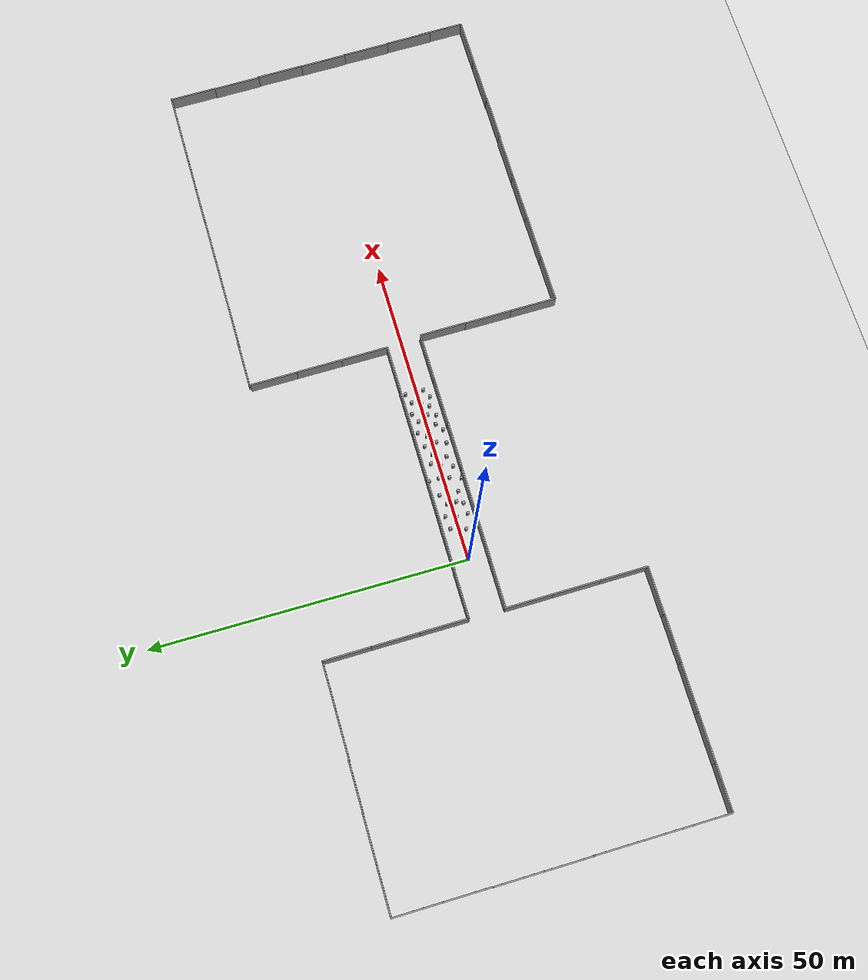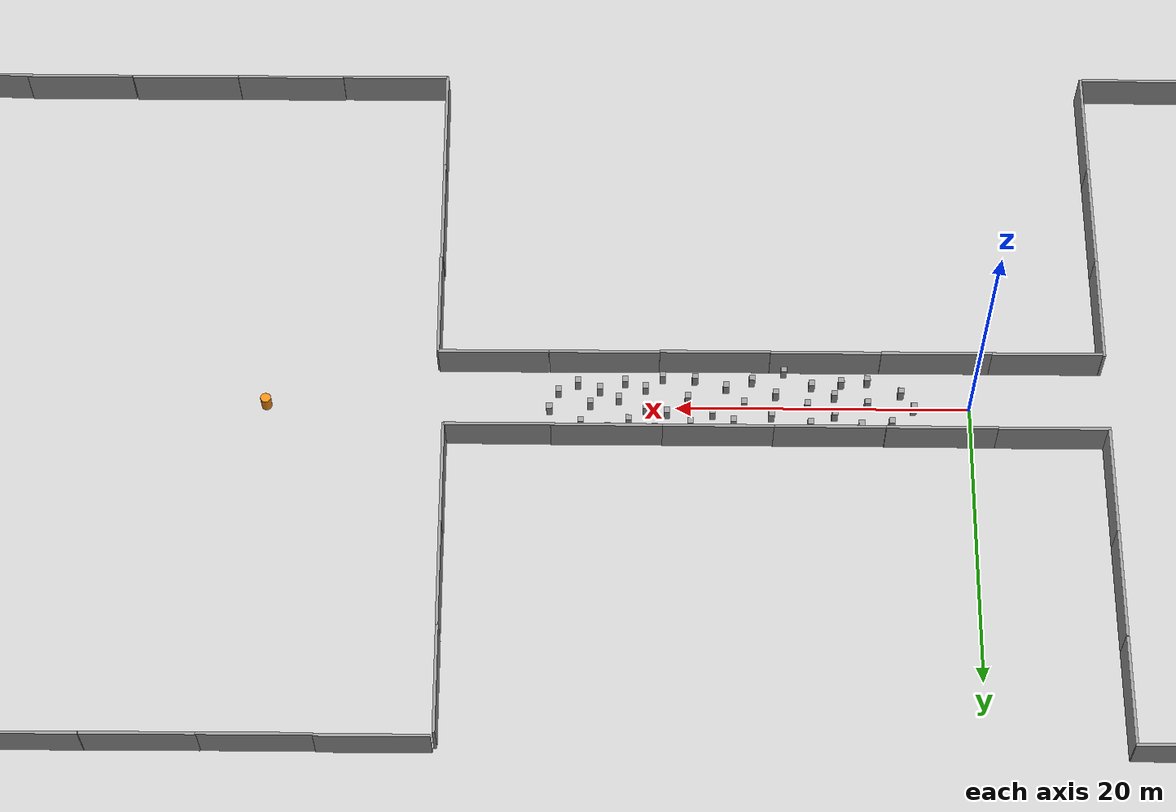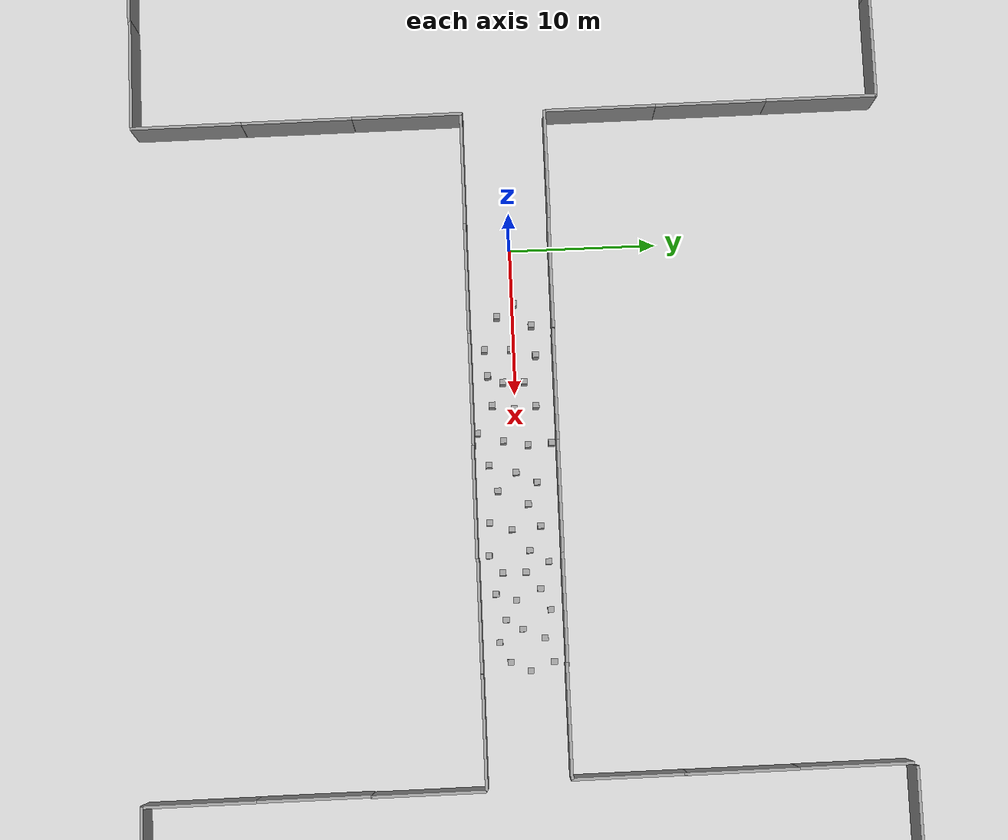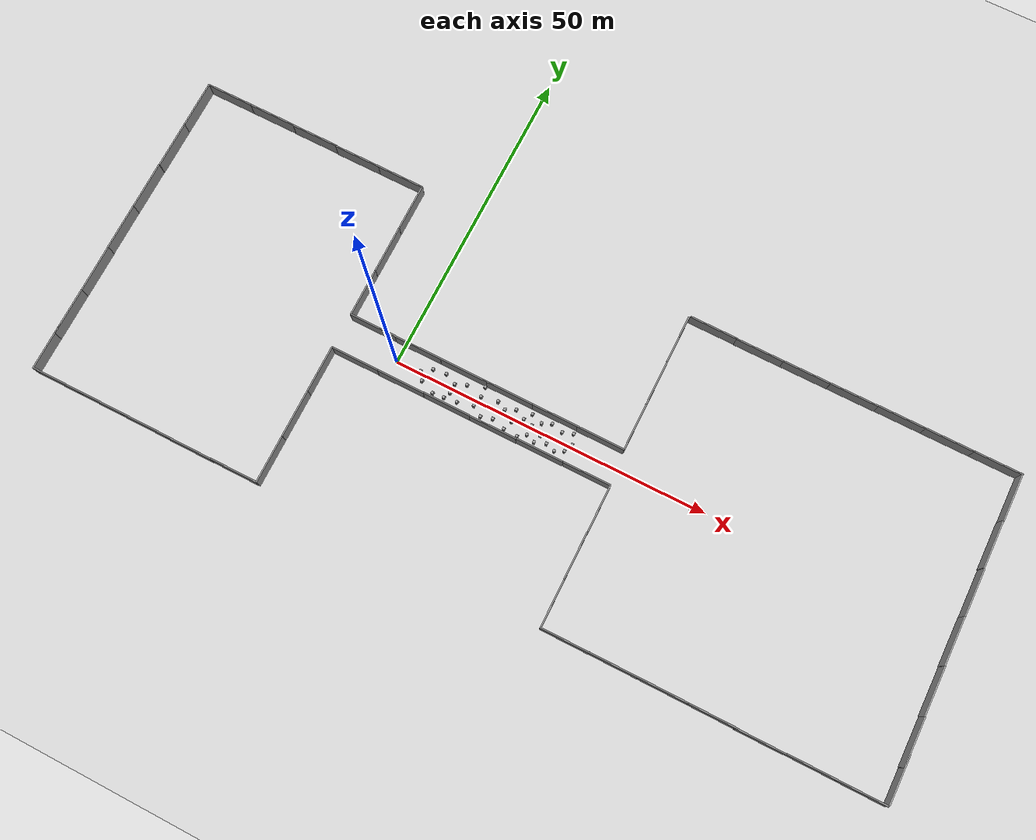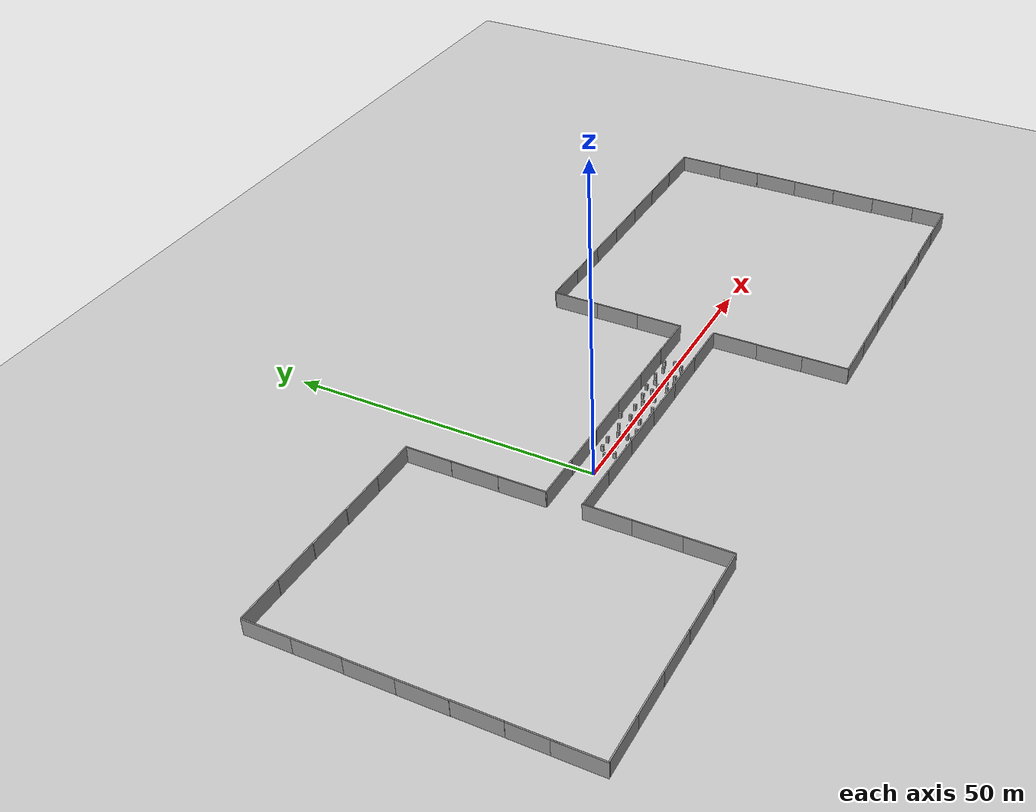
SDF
<?xml version="1.0" ?>
<sdf version='1.10'>
  <world name='obstacle_corridor'>
    <plugin name='gz::sim::systems::Physics' filename='gz-sim-physics-system'/>
    <plugin name='gz::sim::systems::Sensors' filename='gz-sim-sensors-system'>
      <render_engine>ogre2</render_engine>
    </plugin>
    <plugin name='gz::sim::systems::Imu' filename='gz-sim-imu-system'/>
    <plugin name='gz::sim::systems::SceneBroadcaster' filename='gz-sim-scene-broadcaster-system'/>
    <plugin name='gz::sim::systems::UserCommands' filename='gz-sim-user-commands-system'/>
    <physics name='default_physics' type='ignored'>
      <max_step_size>0.001</max_step_size>
      <real_time_factor>0.10000000000000001</real_time_factor>
      <real_time_update_rate>100</real_time_update_rate>
    </physics>
    <scene>
      <ambient>0.400000006 0.400000006 0.400000006 1</ambient>
      <background>0.699999988 0.699999988 0.699999988 1</background>
      <shadows>false</shadows>
    </scene>
    <gravity>0 0 -9.8000000000000007</gravity>
    <magnetic_field>5.6450000000000002e-06 2.2875799999999999e-05 -4.2388400000000002e-05</magnetic_field>
    <atmosphere type='adiabatic'/>
    <audio>
      <device>default</device>
    </audio>
    <wind/>
    <model name='ground_plane'>
      <static>true</static>
      <link name='link'>
        <collision name='collision'>
          <geometry>
            <plane>
              <normal>0 0 1</normal>
              <size>100 100</size>
            </plane>
          </geometry>
          <surface>
            <friction>
              <ode>
                <mu>1000</mu>
                <mu2>1000</mu2>
                <slip1>0</slip1>
                <slip2>0</slip2>
              </ode>
            </friction>
            <bounce/>
            <contact/>
          </surface>
        </collision>
        <visual name='visual'>
          <cast_shadows>false</cast_shadows>
          <geometry>
            <plane>
              <normal>0 0 1</normal>
              <size>100 100</size>
            </plane>
          </geometry>
          <material>
            <script>
              <uri>file://media/materials/scripts/gazebo.material</uri>
              <name>Gazebo/Grey</name>
            </script>
          </material>
        </visual>
        <pose>0 0 0 0 0 0</pose>
        <inertial>
          <pose>0 0 0 0 0 0</pose>
          <mass>1</mass>
          <inertia>
            <ixx>1</ixx>
            <ixy>0</ixy>
            <ixz>0</ixz>
            <iyy>1</iyy>
            <iyz>0</iyz>
            <izz>1</izz>
          </inertia>
        </inertial>
        <enable_wind>false</enable_wind>
      </link>
      <pose>0 0 0 0 0 0</pose>
      <self_collide>false</self_collide>
    </model>
    <model name='grey_wall'>
      <static>true</static>
      <link name='link'>
        <pose>0 0 1.3999999999999999 0 0 0</pose>
        <collision name='collision'>
          <geometry>
            <box>
              <size>7.5 0.20000000000000001 2.7999999999999998</size>
            </box>
          </geometry>
          <max_contacts>10</max_contacts>
          <surface>
            <bounce/>
            <friction>
              <ode/>
              <torsional>
                <ode/>
              </torsional>
            </friction>
            <contact>
              <ode/>
            </contact>
          </surface>
        </collision>
        <visual name='visual'>
          <cast_shadows>false</cast_shadows>
          <geometry>
            <box>
              <size>7.5 0.20000000000000001 2.7999999999999998</size>
            </box>
          </geometry>
          <material>
            <script>
              <name>Gazebo/Grey</name>
              <uri>file://media/materials/scripts/gazebo.material</uri>
            </script>
          </material>
        </visual>
        <velocity_decay>
          <linear>0</linear>
          <angular>0</angular>
        </velocity_decay>
        <self_collide>false</self_collide>
        <kinematic>false</kinematic>
        <gravity>true</gravity>
        <enable_wind>false</enable_wind>
        <inertial>
          <pose>0 0 0 0 0 0</pose>
          <mass>1</mass>
          <inertia>
            <ixx>1</ixx>
            <ixy>0</ixy>
            <ixz>0</ixz>
            <iyy>1</iyy>
            <iyz>0</iyz>
            <izz>1</izz>
          </inertia>
        </inertial>
      </link>
      <pose>17.187099456787109 2.7045242786407471 0 0 0 0</pose>
      <static>true</static>
      <self_collide>false</self_collide>
    </model>
    <model name='grey_wall_0'>
      <static>true</static>
      <link name='link'>
        <pose>0 0 1.3999999999999999 0 0 0</pose>
        <collision name='collision'>
          <geometry>
            <box>
              <size>7.5 0.20000000000000001 2.7999999999999998</size>
            </box>
          </geometry>
          <max_contacts>10</max_contacts>
          <surface>
            <bounce/>
            <friction>
              <ode/>
              <torsional>
                <ode/>
              </torsional>
            </friction>
            <contact>
              <ode/>
            </contact>
          </surface>
        </collision>
        <visual name='visual'>
          <cast_shadows>false</cast_shadows>
          <geometry>
            <box>
              <size>7.5 0.20000000000000001 2.7999999999999998</size>
            </box>
          </geometry>
          <material>
            <script>
              <name>Gazebo/Grey</name>
              <uri>file://media/materials/scripts/gazebo.material</uri>
            </script>
          </material>
        </visual>
        <velocity_decay>
          <linear>0</linear>
          <angular>0</angular>
        </velocity_decay>
        <self_collide>false</self_collide>
        <kinematic>false</kinematic>
        <gravity>true</gravity>
        <enable_wind>false</enable_wind>
        <inertial>
          <pose>0 0 0 0 0 0</pose>
          <mass>1</mass>
          <inertia>
            <ixx>1</ixx>
            <ixy>0</ixy>
            <ixz>0</ixz>
            <iyy>1</iyy>
            <iyz>0</iyz>
            <izz>1</izz>
          </inertia>
        </inertial>
      </link>
      <pose>17.363399505615234 -2.9447300434112549 0 0 0 0</pose>
      <static>true</static>
      <self_collide>false</self_collide>
    </model>
    <model name='grey_wall_clone'>
      <static>true</static>
      <link name='link'>
        <pose>0 0 1.3999999999999999 0 0 0</pose>
        <collision name='collision'>
          <geometry>
            <box>
              <size>7.5 0.20000000000000001 2.7999999999999998</size>
            </box>
          </geometry>
          <max_contacts>10</max_contacts>
          <surface>
            <bounce/>
            <friction>
              <ode/>
              <torsional>
                <ode/>
              </torsional>
            </friction>
            <contact>
              <ode/>
            </contact>
          </surface>
        </collision>
        <visual name='visual'>
          <cast_shadows>false</cast_shadows>
          <geometry>
            <box>
              <size>7.5 0.20000000000000001 2.7999999999999998</size>
            </box>
          </geometry>
          <material>
            <script>
              <name>Gazebo/Grey</name>
              <uri>file://media/materials/scripts/gazebo.material</uri>
            </script>
          </material>
        </visual>
        <velocity_decay>
          <linear>0</linear>
          <angular>0</angular>
        </velocity_decay>
        <self_collide>false</self_collide>
        <kinematic>false</kinematic>
        <gravity>true</gravity>
        <enable_wind>false</enable_wind>
        <inertial>
          <pose>0 0 0 0 0 0</pose>
          <mass>1</mass>
          <inertia>
            <ixx>1</ixx>
            <ixy>0</ixy>
            <ixz>0</ixz>
            <iyy>1</iyy>
            <iyz>0</iyz>
            <izz>1</izz>
          </inertia>
        </inertial>
      </link>
      <pose>2.1738317012786865 2.7372899055480957 0 0 0 0</pose>
      <static>true</static>
      <self_collide>false</self_collide>
    </model>
    <model name='grey_wall_clone_0'>
      <static>true</static>
      <link name='link'>
        <pose>0 0 1.3999999999999999 0 0 0</pose>
        <collision name='collision'>
          <geometry>
            <box>
              <size>7.5 0.20000000000000001 2.7999999999999998</size>
            </box>
          </geometry>
          <max_contacts>10</max_contacts>
          <surface>
            <bounce/>
            <friction>
              <ode/>
              <torsional>
                <ode/>
              </torsional>
            </friction>
            <contact>
              <ode/>
            </contact>
          </surface>
        </collision>
        <visual name='visual'>
          <cast_shadows>false</cast_shadows>
          <geometry>
            <box>
              <size>7.5 0.20000000000000001 2.7999999999999998</size>
            </box>
          </geometry>
          <material>
            <script>
              <name>Gazebo/Grey</name>
              <uri>file://media/materials/scripts/gazebo.material</uri>
            </script>
          </material>
        </visual>
        <velocity_decay>
          <linear>0</linear>
          <angular>0</angular>
        </velocity_decay>
        <self_collide>false</self_collide>
        <kinematic>false</kinematic>
        <gravity>true</gravity>
        <enable_wind>false</enable_wind>
        <inertial>
          <pose>0 0 0 0 0 0</pose>
          <mass>1</mass>
          <inertia>
            <ixx>1</ixx>
            <ixy>0</ixy>
            <ixz>0</ixz>
            <iyy>1</iyy>
            <iyz>0</iyz>
            <izz>1</izz>
          </inertia>
        </inertial>
      </link>
      <pose>2.3360300064086914 -2.9230217933654785 0 0 0 0</pose>
      <static>true</static>
      <self_collide>false</self_collide>
    </model>
    <model name='grey_wall_clone_1'>
      <static>true</static>
      <link name='link'>
        <pose>0 0 1.3999999999999999 0 0 0</pose>
        <collision name='collision'>
          <geometry>
            <box>
              <size>7.5 0.20000000000000001 2.7999999999999998</size>
            </box>
          </geometry>
          <max_contacts>10</max_contacts>
          <surface>
            <bounce/>
            <friction>
              <ode/>
              <torsional>
                <ode/>
              </torsional>
            </friction>
            <contact>
              <ode/>
            </contact>
          </surface>
        </collision>
        <visual name='visual'>
          <cast_shadows>false</cast_shadows>
          <geometry>
            <box>
              <size>7.5 0.20000000000000001 2.7999999999999998</size>
            </box>
          </geometry>
          <material>
            <script>
              <name>Gazebo/Grey</name>
              <uri>file://media/materials/scripts/gazebo.material</uri>
            </script>
          </material>
        </visual>
        <velocity_decay>
          <linear>0</linear>
          <angular>0</angular>
        </velocity_decay>
        <self_collide>false</self_collide>
        <kinematic>false</kinematic>
        <gravity>true</gravity>
        <enable_wind>false</enable_wind>
        <inertial>
          <pose>0 0 0 0 0 0</pose>
          <mass>1</mass>
          <inertia>
            <ixx>1</ixx>
            <ixy>0</ixy>
            <ixz>0</ixz>
            <iyy>1</iyy>
            <iyz>0</iyz>
            <izz>1</izz>
          </inertia>
        </inertial>
      </link>
      <pose>9.8578472137451172 -2.9056301116943359 0 0 0 0</pose>
      <static>true</static>
      <self_collide>false</self_collide>
    </model>
    <model name='grey_wall_clone_2'>
      <static>true</static>
      <link name='link'>
        <pose>0 0 1.3999999999999999 0 0 0</pose>
        <collision name='collision'>
          <geometry>
            <box>
              <size>7.5 0.20000000000000001 2.7999999999999998</size>
            </box>
          </geometry>
          <max_contacts>10</max_contacts>
          <surface>
            <bounce/>
            <friction>
              <ode/>
              <torsional>
                <ode/>
              </torsional>
            </friction>
            <contact>
              <ode/>
            </contact>
          </surface>
        </collision>
        <visual name='visual'>
          <cast_shadows>false</cast_shadows>
          <geometry>
            <box>
              <size>7.5 0.20000000000000001 2.7999999999999998</size>
            </box>
          </geometry>
          <material>
            <script>
              <name>Gazebo/Grey</name>
              <uri>file://media/materials/scripts/gazebo.material</uri>
            </script>
          </material>
        </visual>
        <velocity_decay>
          <linear>0</linear>
          <angular>0</angular>
        </velocity_decay>
        <self_collide>false</self_collide>
        <kinematic>false</kinematic>
        <gravity>true</gravity>
        <enable_wind>false</enable_wind>
        <inertial>
          <pose>0 0 0 0 0 0</pose>
          <mass>1</mass>
          <inertia>
            <ixx>1</ixx>
            <ixy>0</ixy>
            <ixz>0</ixz>
            <iyy>1</iyy>
            <iyz>0</iyz>
            <izz>1</izz>
          </inertia>
        </inertial>
      </link>
      <pose>9.7113351821899414 2.7117300033569336 0 0 0 0</pose>
      <static>true</static>
      <self_collide>false</self_collide>
    </model>
    <model name='grey_wall_clone_3'>
      <static>true</static>
      <link name='link'>
        <pose>0 0 1.3999999999999999 0 0 0</pose>
        <collision name='collision'>
          <geometry>
            <box>
              <size>7.5 0.20000000000000001 2.7999999999999998</size>
            </box>
          </geometry>
          <max_contacts>10</max_contacts>
          <surface>
            <bounce/>
            <friction>
              <ode/>
              <torsional>
                <ode/>
              </torsional>
            </friction>
            <contact>
              <ode/>
            </contact>
          </surface>
        </collision>
        <visual name='visual'>
          <cast_shadows>false</cast_shadows>
          <geometry>
            <box>
              <size>7.5 0.20000000000000001 2.7999999999999998</size>
            </box>
          </geometry>
          <material>
            <script>
              <name>Gazebo/Grey</name>
              <uri>file://media/materials/scripts/gazebo.material</uri>
            </script>
          </material>
        </visual>
        <velocity_decay>
          <linear>0</linear>
          <angular>0</angular>
        </velocity_decay>
        <self_collide>false</self_collide>
        <kinematic>false</kinematic>
        <gravity>true</gravity>
        <enable_wind>false</enable_wind>
        <inertial>
          <pose>0 0 0 0 0 0</pose>
          <mass>1</mass>
          <inertia>
            <ixx>1</ixx>
            <ixy>0</ixy>
            <ixz>0</ixz>
            <iyy>1</iyy>
            <iyz>0</iyz>
            <izz>1</izz>
          </inertia>
        </inertial>
      </link>
      <pose>24.683599472045898 2.6915173530578613 0 0 0 0</pose>
      <static>true</static>
      <self_collide>false</self_collide>
    </model>
    <model name='grey_wall_clone_4'>
      <static>true</static>
      <link name='link'>
        <pose>0 0 1.3999999999999999 0 0 0</pose>
        <collision name='collision'>
          <geometry>
            <box>
              <size>7.5 0.20000000000000001 2.7999999999999998</size>
            </box>
          </geometry>
          <max_contacts>10</max_contacts>
          <surface>
            <bounce/>
            <friction>
              <ode/>
              <torsional>
                <ode/>
              </torsional>
            </friction>
            <contact>
              <ode/>
            </contact>
          </surface>
        </collision>
        <visual name='visual'>
          <cast_shadows>false</cast_shadows>
          <geometry>
            <box>
              <size>7.5 0.20000000000000001 2.7999999999999998</size>
            </box>
          </geometry>
          <material>
            <script>
              <name>Gazebo/Grey</name>
              <uri>file://media/materials/scripts/gazebo.material</uri>
            </script>
          </material>
        </visual>
        <velocity_decay>
          <linear>0</linear>
          <angular>0</angular>
        </velocity_decay>
        <self_collide>false</self_collide>
        <kinematic>false</kinematic>
        <gravity>true</gravity>
        <enable_wind>false</enable_wind>
        <inertial>
          <pose>0 0 0 0 0 0</pose>
          <mass>1</mass>
          <inertia>
            <ixx>1</ixx>
            <ixy>0</ixy>
            <ixz>0</ixz>
            <iyy>1</iyy>
            <iyz>0</iyz>
            <izz>1</izz>
          </inertia>
        </inertial>
      </link>
      <pose>24.86754035949707 -2.9010400772094727 0 0 0 0</pose>
      <static>true</static>
      <self_collide>false</self_collide>
    </model>
    <model name='unit_box_0_clone'>
      <static>true</static>
      <pose>5.3421688079833984 1.2851343154907229 0.49999958276748657 2.0000003746328715e-06 1.0000002420493865e-06 -0.00051600009686087638</pose>
      <link name='link'>
        <inertial>
          <mass>1</mass>
          <inertia>
            <ixx>0.16666700000000001</ixx>
            <ixy>0</ixy>
            <ixz>0</ixz>
            <iyy>0.16666700000000001</iyy>
            <iyz>0</iyz>
            <izz>0.16666700000000001</izz>
          </inertia>
          <pose>0 0 0 0 0 0</pose>
        </inertial>
        <collision name='collision'>
          <geometry>
            <box>
              <size>0.392878 0.42264299999999999 1</size>
            </box>
          </geometry>
          <max_contacts>10</max_contacts>
          <surface>
            <contact>
              <ode/>
            </contact>
            <bounce/>
            <friction>
              <torsional>
                <ode/>
              </torsional>
              <ode/>
            </friction>
          </surface>
        </collision>
        <visual name='visual'>
          <geometry>
            <box>
              <size>0.392878 0.42264299999999999 1</size>
            </box>
          </geometry>
          <material>
            <script>
              <name>Gazebo/Grey</name>
              <uri>file://media/materials/scripts/gazebo.material</uri>
            </script>
          </material>
        </visual>
        <self_collide>false</self_collide>
        <kinematic>false</kinematic>
        <gravity>true</gravity>
        <enable_wind>false</enable_wind>
        <pose>0 0 0 0 0 0</pose>
      </link>
      <static>true</static>
      <self_collide>false</self_collide>
    </model>
    <model name='unit_box_0_clone_3'>
      <static>true</static>
      <pose>9.2073688507080043 0.6758156418800354 0.50000137090682983 -3.0000009789918248e-06 -4.000000824194933e-06 -0.00054700010822561864</pose>
      <link name='link'>
        <inertial>
          <mass>1</mass>
          <inertia>
            <ixx>0.16666700000000001</ixx>
            <ixy>0</ixy>
            <ixz>0</ixz>
            <iyy>0.16666700000000001</iyy>
            <iyz>0</iyz>
            <izz>0.16666700000000001</izz>
          </inertia>
          <pose>0 0 0 0 0 0</pose>
        </inertial>
        <collision name='collision'>
          <geometry>
            <box>
              <size>0.392878 0.42264299999999999 1</size>
            </box>
          </geometry>
          <max_contacts>10</max_contacts>
          <surface>
            <contact>
              <ode/>
            </contact>
            <bounce/>
            <friction>
              <torsional>
                <ode/>
              </torsional>
              <ode/>
            </friction>
          </surface>
        </collision>
        <visual name='visual'>
          <geometry>
            <box>
              <size>0.392878 0.42264299999999999 1</size>
            </box>
          </geometry>
          <material>
            <script>
              <name>Gazebo/Grey</name>
              <uri>file://media/materials/scripts/gazebo.material</uri>
            </script>
          </material>
        </visual>
        <self_collide>false</self_collide>
        <kinematic>false</kinematic>
        <gravity>true</gravity>
        <enable_wind>false</enable_wind>
        <pose>0 0 0 0 0 0</pose>
      </link>
      <static>true</static>
      <self_collide>false</self_collide>
    </model>
    <model name='unit_box_0_clone_5_clone_0'>
      <static>true</static>
      <pose>7.4106899999999998 1.50068 0.50000100000000003 -1.0000001187337507e-06 -2.0000002376448185e-06 -0.00059700007092639462</pose>
      <link name='link'>
        <inertial>
          <mass>1</mass>
          <inertia>
            <ixx>0.16666700000000001</ixx>
            <ixy>0</ixy>
            <ixz>0</ixz>
            <iyy>0.16666700000000001</iyy>
            <iyz>0</iyz>
            <izz>0.16666700000000001</izz>
          </inertia>
          <pose>0 0 0 0 0 0</pose>
        </inertial>
        <collision name='collision'>
          <geometry>
            <box>
              <size>0.392878 0.42264299999999999 1</size>
            </box>
          </geometry>
          <max_contacts>10</max_contacts>
          <surface>
            <contact>
              <ode/>
            </contact>
            <bounce/>
            <friction>
              <torsional>
                <ode/>
              </torsional>
              <ode/>
            </friction>
          </surface>
        </collision>
        <visual name='visual'>
          <geometry>
            <box>
              <size>0.392878 0.42264299999999999 1</size>
            </box>
          </geometry>
          <material>
            <script>
              <name>Gazebo/Grey</name>
              <uri>file://media/materials/scripts/gazebo.material</uri>
            </script>
          </material>
        </visual>
        <self_collide>false</self_collide>
        <kinematic>false</kinematic>
        <gravity>true</gravity>
        <enable_wind>false</enable_wind>
        <pose>0 0 0 0 0 0</pose>
      </link>
      <static>true</static>
      <self_collide>false</self_collide>
    </model>
    <model name='unit_box_0_clone_5_clone_2'>
      <static>true</static>
      <pose>9.1869499999999995 -0.79958200000000001 0.50000100000000003 -2.0000002489220385e-06 1.0000001243659773e-06 -0.00061100007603407161</pose>
      <link name='link'>
        <inertial>
          <mass>1</mass>
          <inertia>
            <ixx>0.16666700000000001</ixx>
            <ixy>0</ixy>
            <ixz>0</ixz>
            <iyy>0.16666700000000001</iyy>
            <iyz>0</iyz>
            <izz>0.16666700000000001</izz>
          </inertia>
          <pose>0 0 0 0 0 0</pose>
        </inertial>
        <collision name='collision'>
          <geometry>
            <box>
              <size>0.392878 0.42264299999999999 1</size>
            </box>
          </geometry>
          <max_contacts>10</max_contacts>
          <surface>
            <contact>
              <ode/>
            </contact>
            <bounce/>
            <friction>
              <torsional>
                <ode/>
              </torsional>
              <ode/>
            </friction>
          </surface>
        </collision>
        <visual name='visual'>
          <geometry>
            <box>
              <size>0.392878 0.42264299999999999 1</size>
            </box>
          </geometry>
          <material>
            <script>
              <name>Gazebo/Grey</name>
              <uri>file://media/materials/scripts/gazebo.material</uri>
            </script>
          </material>
        </visual>
        <self_collide>false</self_collide>
        <kinematic>false</kinematic>
        <gravity>true</gravity>
        <enable_wind>false</enable_wind>
        <pose>0 0 0 0 0 0</pose>
      </link>
      <static>true</static>
      <self_collide>false</self_collide>
    </model>
    <model name='unit_box_0_clone_5_clone_2_clone'>
      <static>true</static>
      <pose>10.729900000000001 -1.5690999999999999 0.50000100000000003 2.0000003900787764e-06 1.0000001952259307e-06 -0.00076500014923367875</pose>
      <link name='link'>
        <inertial>
          <mass>1</mass>
          <inertia>
            <ixx>0.16666700000000001</ixx>
            <ixy>0</ixy>
            <ixz>0</ixz>
            <iyy>0.16666700000000001</iyy>
            <iyz>0</iyz>
            <izz>0.16666700000000001</izz>
          </inertia>
          <pose>0 0 0 0 0 0</pose>
        </inertial>
        <collision name='collision'>
          <geometry>
            <box>
              <size>0.392878 0.42264299999999999 1</size>
            </box>
          </geometry>
          <max_contacts>10</max_contacts>
          <surface>
            <contact>
              <ode/>
            </contact>
            <bounce/>
            <friction>
              <torsional>
                <ode/>
              </torsional>
              <ode/>
            </friction>
          </surface>
        </collision>
        <visual name='visual'>
          <geometry>
            <box>
              <size>0.392878 0.42264299999999999 1</size>
            </box>
          </geometry>
          <material>
            <script>
              <name>Gazebo/Grey</name>
              <uri>file://media/materials/scripts/gazebo.material</uri>
            </script>
          </material>
        </visual>
        <self_collide>false</self_collide>
        <kinematic>false</kinematic>
        <gravity>true</gravity>
        <enable_wind>false</enable_wind>
        <pose>0 0 0 0 0 0</pose>
      </link>
      <static>true</static>
      <self_collide>false</self_collide>
    </model>
    <model name='unit_box_0_clone_5_clone_2_clone_0'>
      <static>true</static>
      <pose>13.505867958068848 0.75421446561813354 0.50000911951065075 -5.0000012668553429e-06 -2.0000004055770497e-06 -0.00078500017208024393</pose>
      <link name='link'>
        <inertial>
          <mass>1</mass>
          <inertia>
            <ixx>0.16666700000000001</ixx>
            <ixy>0</ixy>
            <ixz>0</ixz>
            <iyy>0.16666700000000001</iyy>
            <iyz>0</iyz>
            <izz>0.16666700000000001</izz>
          </inertia>
          <pose>0 0 0 0 0 0</pose>
        </inertial>
        <collision name='collision'>
          <geometry>
            <box>
              <size>0.392878 0.42264299999999999 1</size>
            </box>
          </geometry>
          <max_contacts>10</max_contacts>
          <surface>
            <contact>
              <ode/>
            </contact>
            <bounce/>
            <friction>
              <torsional>
                <ode/>
              </torsional>
              <ode/>
            </friction>
          </surface>
        </collision>
        <visual name='visual'>
          <geometry>
            <box>
              <size>0.392878 0.42264299999999999 1</size>
            </box>
          </geometry>
          <material>
            <script>
              <name>Gazebo/Grey</name>
              <uri>file://media/materials/scripts/gazebo.material</uri>
            </script>
          </material>
        </visual>
        <self_collide>false</self_collide>
        <kinematic>false</kinematic>
        <gravity>true</gravity>
        <enable_wind>false</enable_wind>
        <pose>0 0 0 0 0 0</pose>
      </link>
      <static>true</static>
      <self_collide>false</self_collide>
    </model>
    <model name='unit_box_0_clone_5_clone_2_clone_1'>
      <static>true</static>
      <pose>4.6627099999999997 -1.0221899999999999 0.50000100000000003 -2.0000003720788588e-06 1.000000185865747e-06 -0.00074700013894551096</pose>
      <link name='link'>
        <inertial>
          <mass>1</mass>
          <inertia>
            <ixx>0.16666700000000001</ixx>
            <ixy>0</ixy>
            <ixz>0</ixz>
            <iyy>0.16666700000000001</iyy>
            <iyz>0</iyz>
            <izz>0.16666700000000001</izz>
          </inertia>
          <pose>0 0 0 0 0 0</pose>
        </inertial>
        <collision name='collision'>
          <geometry>
            <box>
              <size>0.392878 0.42264299999999999 1</size>
            </box>
          </geometry>
          <max_contacts>10</max_contacts>
          <surface>
            <contact>
              <ode/>
            </contact>
            <bounce/>
            <friction>
              <torsional>
                <ode/>
              </torsional>
              <ode/>
            </friction>
          </surface>
        </collision>
        <visual name='visual'>
          <geometry>
            <box>
              <size>0.392878 0.42264299999999999 1</size>
            </box>
          </geometry>
          <material>
            <script>
              <name>Gazebo/Grey</name>
              <uri>file://media/materials/scripts/gazebo.material</uri>
            </script>
          </material>
        </visual>
        <self_collide>false</self_collide>
        <kinematic>false</kinematic>
        <gravity>true</gravity>
        <enable_wind>false</enable_wind>
        <pose>0 0 0 0 0 0</pose>
      </link>
      <static>true</static>
      <self_collide>false</self_collide>
    </model>
    <model name='unit_box_0_clone_5_clone_2_clone_2'>
      <static>true</static>
      <pose>3.8238189220428471 0.15667788684368128 0.50000017881393422 -2.00000028844333e-06 1.0000002078150583e-06 -0.00072900011429083834</pose>
      <link name='link'>
        <inertial>
          <mass>1</mass>
          <inertia>
            <ixx>0.16666700000000001</ixx>
            <ixy>0</ixy>
            <ixz>0</ixz>
            <iyy>0.16666700000000001</iyy>
            <iyz>0</iyz>
            <izz>0.16666700000000001</izz>
          </inertia>
          <pose>0 0 0 0 0 0</pose>
        </inertial>
        <collision name='collision'>
          <geometry>
            <box>
              <size>0.392878 0.42264299999999999 1</size>
            </box>
          </geometry>
          <max_contacts>10</max_contacts>
          <surface>
            <contact>
              <ode/>
            </contact>
            <bounce/>
            <friction>
              <torsional>
                <ode/>
              </torsional>
              <ode/>
            </friction>
          </surface>
        </collision>
        <visual name='visual'>
          <geometry>
            <box>
              <size>0.392878 0.42264299999999999 1</size>
            </box>
          </geometry>
          <material>
            <script>
              <name>Gazebo/Grey</name>
              <uri>file://media/materials/scripts/gazebo.material</uri>
            </script>
          </material>
        </visual>
        <self_collide>false</self_collide>
        <kinematic>false</kinematic>
        <gravity>true</gravity>
        <enable_wind>false</enable_wind>
        <pose>0 0 0 0 0 0</pose>
      </link>
      <static>true</static>
      <self_collide>false</self_collide>
    </model>
    <model name='unit_box_0_clone_5_clone_2_clone_4'>
      <static>true</static>
      <pose>11.022399999999999 -0.071739999999999998 0.50000100000000003 2.000000379810199e-06 3.0000005701815457e-06 -0.0007550001434595907</pose>
      <link name='link'>
        <inertial>
          <mass>1</mass>
          <inertia>
            <ixx>0.16666700000000001</ixx>
            <ixy>0</ixy>
            <ixz>0</ixz>
            <iyy>0.16666700000000001</iyy>
            <iyz>0</iyz>
            <izz>0.16666700000000001</izz>
          </inertia>
          <pose>0 0 0 0 0 0</pose>
        </inertial>
        <collision name='collision'>
          <geometry>
            <box>
              <size>0.392878 0.42264299999999999 1</size>
            </box>
          </geometry>
          <max_contacts>10</max_contacts>
          <surface>
            <contact>
              <ode/>
            </contact>
            <bounce/>
            <friction>
              <torsional>
                <ode/>
              </torsional>
              <ode/>
            </friction>
          </surface>
        </collision>
        <visual name='visual'>
          <geometry>
            <box>
              <size>0.392878 0.42264299999999999 1</size>
            </box>
          </geometry>
          <material>
            <script>
              <name>Gazebo/Grey</name>
              <uri>file://media/materials/scripts/gazebo.material</uri>
            </script>
          </material>
        </visual>
        <self_collide>false</self_collide>
        <kinematic>false</kinematic>
        <gravity>true</gravity>
        <enable_wind>false</enable_wind>
        <pose>0 0 0 0 0 0</pose>
      </link>
      <static>true</static>
      <self_collide>false</self_collide>
    </model>
    <model name='unit_box_0_clone_5_clone_2_clone_5'>
      <static>true</static>
      <pose>12.612545013427731 -2.6441345214843754 0.50000119209289551 -2.0000002923725765e-06 1.0000001559271868e-06 -0.00063200007067366296</pose>
      <link name='link'>
        <inertial>
          <mass>1</mass>
          <inertia>
            <ixx>0.16666700000000001</ixx>
            <ixy>0</ixy>
            <ixz>0</ixz>
            <iyy>0.16666700000000001</iyy>
            <iyz>0</iyz>
            <izz>0.16666700000000001</izz>
          </inertia>
          <pose>0 0 0 0 0 0</pose>
        </inertial>
        <collision name='collision'>
          <geometry>
            <box>
              <size>0.392878 0.42264299999999999 1</size>
            </box>
          </geometry>
          <max_contacts>10</max_contacts>
          <surface>
            <contact>
              <ode/>
            </contact>
            <bounce/>
            <friction>
              <torsional>
                <ode/>
              </torsional>
              <ode/>
            </friction>
          </surface>
        </collision>
        <visual name='visual'>
          <geometry>
            <box>
              <size>0.392878 0.42264299999999999 1</size>
            </box>
          </geometry>
          <material>
            <script>
              <name>Gazebo/Grey</name>
              <uri>file://media/materials/scripts/gazebo.material</uri>
            </script>
          </material>
        </visual>
        <self_collide>false</self_collide>
        <kinematic>false</kinematic>
        <gravity>true</gravity>
        <enable_wind>false</enable_wind>
        <pose>0 0 0 0 0 0</pose>
      </link>
      <static>true</static>
      <self_collide>false</self_collide>
    </model>
    <model name='unit_box_0_clone_5_clone_2_clone_6'>
      <static>true</static>
      <pose>13.1767 -0.89563199999999998 0.5 -1.000000126564928e-06 2.0000002529350668e-06 -0.00061600007791600168</pose>
      <link name='link'>
        <inertial>
          <mass>1</mass>
          <inertia>
            <ixx>0.16666700000000001</ixx>
            <ixy>0</ixy>
            <ixz>0</ixz>
            <iyy>0.16666700000000001</iyy>
            <iyz>0</iyz>
            <izz>0.16666700000000001</izz>
          </inertia>
          <pose>0 0 0 0 0 0</pose>
        </inertial>
        <collision name='collision'>
          <geometry>
            <box>
              <size>0.392878 0.42264299999999999 1</size>
            </box>
          </geometry>
          <max_contacts>10</max_contacts>
          <surface>
            <contact>
              <ode/>
            </contact>
            <bounce/>
            <friction>
              <torsional>
                <ode/>
              </torsional>
              <ode/>
            </friction>
          </surface>
        </collision>
        <visual name='visual'>
          <geometry>
            <box>
              <size>0.392878 0.42264299999999999 1</size>
            </box>
          </geometry>
          <material>
            <script>
              <name>Gazebo/Grey</name>
              <uri>file://media/materials/scripts/gazebo.material</uri>
            </script>
          </material>
        </visual>
        <self_collide>false</self_collide>
        <kinematic>false</kinematic>
        <gravity>true</gravity>
        <enable_wind>false</enable_wind>
        <pose>0 0 0 0 0 0</pose>
      </link>
      <static>true</static>
      <self_collide>false</self_collide>
    </model>
    <model name='unit_box_0_clone_3_clone_3'>
      <static>true</static>
      <pose>8.7023399999999995 -1.7966200000000001 0.50000100000000003 2.0000005678250643e-06 1.0000002842401721e-06 -0.00092300026211176772</pose>
      <link name='link'>
        <inertial>
          <mass>1</mass>
          <inertia>
            <ixx>0.16666700000000001</ixx>
            <ixy>0</ixy>
            <ixz>0</ixz>
            <iyy>0.16666700000000001</iyy>
            <iyz>0</iyz>
            <izz>0.16666700000000001</izz>
          </inertia>
          <pose>0 0 0 0 0 0</pose>
        </inertial>
        <collision name='collision'>
          <geometry>
            <box>
              <size>0.392878 0.42264299999999999 1</size>
            </box>
          </geometry>
          <max_contacts>10</max_contacts>
          <surface>
            <contact>
              <ode/>
            </contact>
            <bounce/>
            <friction>
              <torsional>
                <ode/>
              </torsional>
              <ode/>
            </friction>
          </surface>
        </collision>
        <visual name='visual'>
          <geometry>
            <box>
              <size>0.392878 0.42264299999999999 1</size>
            </box>
          </geometry>
          <material>
            <script>
              <name>Gazebo/Grey</name>
              <uri>file://media/materials/scripts/gazebo.material</uri>
            </script>
          </material>
        </visual>
        <self_collide>false</self_collide>
        <kinematic>false</kinematic>
        <gravity>true</gravity>
        <enable_wind>false</enable_wind>
        <pose>0 0 0 0 0 0</pose>
      </link>
      <static>true</static>
      <self_collide>false</self_collide>
    </model>
    <model name='unit_box_0_clone_3_clone_5'>
      <static>true</static>
      <pose>6.9551668167114258 -0.18439726531505585 0.49999991059303273 5.0000016584703958e-06 2.0000006920003074e-06 -0.0009740003068479902</pose>
      <link name='link'>
        <inertial>
          <mass>1</mass>
          <inertia>
            <ixx>0.16666700000000001</ixx>
            <ixy>0</ixy>
            <ixz>0</ixz>
            <iyy>0.16666700000000001</iyy>
            <iyz>0</iyz>
            <izz>0.16666700000000001</izz>
          </inertia>
          <pose>0 0 0 0 0 0</pose>
        </inertial>
        <collision name='collision'>
          <geometry>
            <box>
              <size>0.392878 0.42264299999999999 1</size>
            </box>
          </geometry>
          <max_contacts>10</max_contacts>
          <surface>
            <contact>
              <ode/>
            </contact>
            <bounce/>
            <friction>
              <torsional>
                <ode/>
              </torsional>
              <ode/>
            </friction>
          </surface>
        </collision>
        <visual name='visual'>
          <geometry>
            <box>
              <size>0.392878 0.42264299999999999 1</size>
            </box>
          </geometry>
          <material>
            <script>
              <name>Gazebo/Grey</name>
              <uri>file://media/materials/scripts/gazebo.material</uri>
            </script>
          </material>
        </visual>
        <self_collide>false</self_collide>
        <kinematic>false</kinematic>
        <gravity>true</gravity>
        <enable_wind>false</enable_wind>
        <pose>0 0 0 0 0 0</pose>
      </link>
      <static>true</static>
      <self_collide>false</self_collide>
    </model>
    <model name='unit_box_0_clone_5_clone_1_clone'>
      <static>true</static>
      <pose>14.789099999999999 -1.94096 0.50000100000000003 1.0000000399208095e-06 -2.0000000798071012e-06 -0.00034600001380782295</pose>
      <link name='link'>
        <inertial>
          <mass>1</mass>
          <inertia>
            <ixx>0.16666700000000001</ixx>
            <ixy>0</ixy>
            <ixz>0</ixz>
            <iyy>0.16666700000000001</iyy>
            <iyz>0</iyz>
            <izz>0.16666700000000001</izz>
          </inertia>
          <pose>0 0 0 0 0 0</pose>
        </inertial>
        <collision name='collision'>
          <geometry>
            <box>
              <size>0.392878 0.42264299999999999 1</size>
            </box>
          </geometry>
          <max_contacts>10</max_contacts>
          <surface>
            <contact>
              <ode/>
            </contact>
            <bounce/>
            <friction>
              <torsional>
                <ode/>
              </torsional>
              <ode/>
            </friction>
          </surface>
        </collision>
        <visual name='visual'>
          <geometry>
            <box>
              <size>0.392878 0.42264299999999999 1</size>
            </box>
          </geometry>
          <material>
            <script>
              <name>Gazebo/Grey</name>
              <uri>file://media/materials/scripts/gazebo.material</uri>
            </script>
          </material>
        </visual>
        <self_collide>false</self_collide>
        <kinematic>false</kinematic>
        <gravity>true</gravity>
        <enable_wind>false</enable_wind>
        <pose>0 0 0 0 0 0</pose>
      </link>
      <static>true</static>
      <self_collide>false</self_collide>
    </model>
    <model name='unit_box_0_clone_5_clone_1_clone_0'>
      <static>true</static>
      <pose>15.339099884033203 -0.13711300492286682 0.50000101327896118 -9.9999995084638834e-07 3.0000000458730671e-06 -0.00034299999056368454</pose>
      <link name='link'>
        <inertial>
          <mass>1</mass>
          <inertia>
            <ixx>0.16666700000000001</ixx>
            <ixy>0</ixy>
            <ixz>0</ixz>
            <iyy>0.16666700000000001</iyy>
            <iyz>0</iyz>
            <izz>0.16666700000000001</izz>
          </inertia>
          <pose>0 0 0 0 0 0</pose>
        </inertial>
        <collision name='collision'>
          <geometry>
            <box>
              <size>0.392878 0.42264299999999999 1</size>
            </box>
          </geometry>
          <max_contacts>10</max_contacts>
          <surface>
            <contact>
              <ode/>
            </contact>
            <bounce/>
            <friction>
              <torsional>
                <ode/>
              </torsional>
              <ode/>
            </friction>
          </surface>
        </collision>
        <visual name='visual'>
          <geometry>
            <box>
              <size>0.392878 0.42264299999999999 1</size>
            </box>
          </geometry>
          <material>
            <script>
              <name>Gazebo/Grey</name>
              <uri>file://media/materials/scripts/gazebo.material</uri>
            </script>
          </material>
        </visual>
        <self_collide>false</self_collide>
        <kinematic>false</kinematic>
        <gravity>true</gravity>
        <enable_wind>false</enable_wind>
        <pose>0 0 0 0 0 0</pose>
      </link>
      <static>true</static>
      <self_collide>false</self_collide>
    </model>
    <model name='unit_box_0_clone_5_clone_1_clone_1'>
      <static>true</static>
      <pose>16.0654 1.24238 0.50000100000000003 -2.0000000699866681e-06 -1.1337840556560594e-17 -0.0003240000113378403</pose>
      <link name='link'>
        <inertial>
          <mass>1</mass>
          <inertia>
            <ixx>0.16666700000000001</ixx>
            <ixy>0</ixy>
            <ixz>0</ixz>
            <iyy>0.16666700000000001</iyy>
            <iyz>0</iyz>
            <izz>0.16666700000000001</izz>
          </inertia>
          <pose>0 0 0 0 0 0</pose>
        </inertial>
        <collision name='collision'>
          <geometry>
            <box>
              <size>0.392878 0.42264299999999999 1</size>
            </box>
          </geometry>
          <max_contacts>10</max_contacts>
          <surface>
            <contact>
              <ode/>
            </contact>
            <bounce/>
            <friction>
              <torsional>
                <ode/>
              </torsional>
              <ode/>
            </friction>
          </surface>
        </collision>
        <visual name='visual'>
          <geometry>
            <box>
              <size>0.392878 0.42264299999999999 1</size>
            </box>
          </geometry>
          <material>
            <script>
              <name>Gazebo/Grey</name>
              <uri>file://media/materials/scripts/gazebo.material</uri>
            </script>
          </material>
        </visual>
        <self_collide>false</self_collide>
        <kinematic>false</kinematic>
        <gravity>true</gravity>
        <enable_wind>false</enable_wind>
        <pose>0 0 0 0 0 0</pose>
      </link>
      <static>true</static>
      <self_collide>false</self_collide>
    </model>
    <model name='unit_box_0_clone_5_clone_1_clone_3'>
      <static>true</static>
      <pose>17.505437850952148 0.59749346971511841 0.4999997615814209 5.8466378305452428e-17 2.9999998787366496e-06 -0.00030799998541884862</pose>
      <link name='link'>
        <inertial>
          <mass>1</mass>
          <inertia>
            <ixx>0.16666700000000001</ixx>
            <ixy>0</ixy>
            <ixz>0</ixz>
            <iyy>0.16666700000000001</iyy>
            <iyz>0</iyz>
            <izz>0.16666700000000001</izz>
          </inertia>
          <pose>0 0 0 0 0 0</pose>
        </inertial>
        <collision name='collision'>
          <geometry>
            <box>
              <size>0.392878 0.42264299999999999 1</size>
            </box>
          </geometry>
          <max_contacts>10</max_contacts>
          <surface>
            <contact>
              <ode/>
            </contact>
            <bounce/>
            <friction>
              <torsional>
                <ode/>
              </torsional>
              <ode/>
            </friction>
          </surface>
        </collision>
        <visual name='visual'>
          <geometry>
            <box>
              <size>0.392878 0.42264299999999999 1</size>
            </box>
          </geometry>
          <material>
            <script>
              <name>Gazebo/Grey</name>
              <uri>file://media/materials/scripts/gazebo.material</uri>
            </script>
          </material>
        </visual>
        <self_collide>false</self_collide>
        <kinematic>false</kinematic>
        <gravity>true</gravity>
        <enable_wind>false</enable_wind>
        <pose>0 0 0 0 0 0</pose>
      </link>
      <static>true</static>
      <self_collide>false</self_collide>
    </model>
    <model name='unit_box_0_clone_5_clone_1_clone_4'>
      <static>true</static>
      <pose>18.672418594360352 -2.0511386394500732 0.49998795986175537 4.9999997545680128e-06 3.0000000014266035e-06 -0.00029899999690716732</pose>
      <link name='link'>
        <inertial>
          <mass>1</mass>
          <inertia>
            <ixx>0.16666700000000001</ixx>
            <ixy>0</ixy>
            <ixz>0</ixz>
            <iyy>0.16666700000000001</iyy>
            <iyz>0</iyz>
            <izz>0.16666700000000001</izz>
          </inertia>
          <pose>0 0 0 0 0 0</pose>
        </inertial>
        <collision name='collision'>
          <geometry>
            <box>
              <size>0.392878 0.42264299999999999 1</size>
            </box>
          </geometry>
          <max_contacts>10</max_contacts>
          <surface>
            <contact>
              <ode/>
            </contact>
            <bounce/>
            <friction>
              <torsional>
                <ode/>
              </torsional>
              <ode/>
            </friction>
          </surface>
        </collision>
        <visual name='visual'>
          <geometry>
            <box>
              <size>0.392878 0.42264299999999999 1</size>
            </box>
          </geometry>
          <material>
            <script>
              <name>Gazebo/Grey</name>
              <uri>file://media/materials/scripts/gazebo.material</uri>
            </script>
          </material>
        </visual>
        <self_collide>false</self_collide>
        <kinematic>false</kinematic>
        <gravity>true</gravity>
        <enable_wind>false</enable_wind>
        <pose>0 0 0 0 0 0</pose>
      </link>
      <static>true</static>
      <self_collide>false</self_collide>
    </model>
    <model name='unit_box_0_clone_5_clone_1_clone_5'>
      <static>true</static>
      <pose>16.557600021362305 -1.4180713891983032 0.49999698996543884 -3.0000000344854799e-06 -2.9999999503741765e-06 -0.00030199999357909124</pose>
      <link name='link'>
        <inertial>
          <mass>1</mass>
          <inertia>
            <ixx>0.16666700000000001</ixx>
            <ixy>0</ixy>
            <ixz>0</ixz>
            <iyy>0.16666700000000001</iyy>
            <iyz>0</iyz>
            <izz>0.16666700000000001</izz>
          </inertia>
          <pose>0 0 0 0 0 0</pose>
        </inertial>
        <collision name='collision'>
          <geometry>
            <box>
              <size>0.392878 0.42264299999999999 1</size>
            </box>
          </geometry>
          <max_contacts>10</max_contacts>
          <surface>
            <contact>
              <ode/>
            </contact>
            <bounce/>
            <friction>
              <torsional>
                <ode/>
              </torsional>
              <ode/>
            </friction>
          </surface>
        </collision>
        <visual name='visual'>
          <geometry>
            <box>
              <size>0.392878 0.42264299999999999 1</size>
            </box>
          </geometry>
          <material>
            <script>
              <name>Gazebo/Grey</name>
              <uri>file://media/materials/scripts/gazebo.material</uri>
            </script>
          </material>
        </visual>
        <self_collide>false</self_collide>
        <kinematic>false</kinematic>
        <gravity>true</gravity>
        <enable_wind>false</enable_wind>
        <pose>0 0 0 0 0 0</pose>
      </link>
      <static>true</static>
      <self_collide>false</self_collide>
    </model>
    <model name='unit_box_0_clone_5_clone_1_clone_13'>
      <static>true</static>
      <pose>20.613299999999999 0.571052 0.49999900000000003 3.0000000882307389e-06 -2.0000000588015679e-06 -0.00029700000873397866</pose>
      <link name='link'>
        <inertial>
          <mass>1</mass>
          <inertia>
            <ixx>0.16666700000000001</ixx>
            <ixy>0</ixy>
            <ixz>0</ixz>
            <iyy>0.16666700000000001</iyy>
            <iyz>0</iyz>
            <izz>0.16666700000000001</izz>
          </inertia>
          <pose>0 0 0 0 0 0</pose>
        </inertial>
        <collision name='collision'>
          <geometry>
            <box>
              <size>0.392878 0.42264299999999999 1</size>
            </box>
          </geometry>
          <max_contacts>10</max_contacts>
          <surface>
            <contact>
              <ode/>
            </contact>
            <bounce/>
            <friction>
              <torsional>
                <ode/>
              </torsional>
              <ode/>
            </friction>
          </surface>
        </collision>
        <visual name='visual'>
          <geometry>
            <box>
              <size>0.392878 0.42264299999999999 1</size>
            </box>
          </geometry>
          <material>
            <script>
              <name>Gazebo/Grey</name>
              <uri>file://media/materials/scripts/gazebo.material</uri>
            </script>
          </material>
        </visual>
        <self_collide>false</self_collide>
        <kinematic>false</kinematic>
        <gravity>true</gravity>
        <enable_wind>false</enable_wind>
        <pose>0 0 0 0 0 0</pose>
      </link>
      <static>true</static>
      <self_collide>false</self_collide>
    </model>
    <model name='unit_box_0_clone_5_clone_1_clone_15'>
      <static>true</static>
      <pose>19.173300000000001 -0.56108100000000005 0.5 1.0000000272698996e-06 -1.0000000272621026e-06 -0.00028600000779807643</pose>
      <link name='link'>
        <inertial>
          <mass>1</mass>
          <inertia>
            <ixx>0.16666700000000001</ixx>
            <ixy>0</ixy>
            <ixz>0</ixz>
            <iyy>0.16666700000000001</iyy>
            <iyz>0</iyz>
            <izz>0.16666700000000001</izz>
          </inertia>
          <pose>0 0 0 0 0 0</pose>
        </inertial>
        <collision name='collision'>
          <geometry>
            <box>
              <size>0.392878 0.42264299999999999 1</size>
            </box>
          </geometry>
          <max_contacts>10</max_contacts>
          <surface>
            <contact>
              <ode/>
            </contact>
            <bounce/>
            <friction>
              <torsional>
                <ode/>
              </torsional>
              <ode/>
            </friction>
          </surface>
        </collision>
        <visual name='visual'>
          <geometry>
            <box>
              <size>0.392878 0.42264299999999999 1</size>
            </box>
          </geometry>
          <material>
            <script>
              <name>Gazebo/Grey</name>
              <uri>file://media/materials/scripts/gazebo.material</uri>
            </script>
          </material>
        </visual>
        <self_collide>false</self_collide>
        <kinematic>false</kinematic>
        <gravity>true</gravity>
        <enable_wind>false</enable_wind>
        <pose>0 0 0 0 0 0</pose>
      </link>
      <static>true</static>
      <self_collide>false</self_collide>
    </model>
    <model name='unit_box_0_clone_5_clone_1_clone_17'>
      <static>true</static>
      <pose>20.865400000000001 -2.1651899999999999 0.50000100000000003 -1.0000000326682239e-06 2.000000065310892e-06 -0.00031300001022195459</pose>
      <link name='link'>
        <inertial>
          <mass>1</mass>
          <inertia>
            <ixx>0.16666700000000001</ixx>
            <ixy>0</ixy>
            <ixz>0</ixz>
            <iyy>0.16666700000000001</iyy>
            <iyz>0</iyz>
            <izz>0.16666700000000001</izz>
          </inertia>
          <pose>0 0 0 0 0 0</pose>
        </inertial>
        <collision name='collision'>
          <geometry>
            <box>
              <size>0.392878 0.42264299999999999 1</size>
            </box>
          </geometry>
          <max_contacts>10</max_contacts>
          <surface>
            <contact>
              <ode/>
            </contact>
            <bounce/>
            <friction>
              <torsional>
                <ode/>
              </torsional>
              <ode/>
            </friction>
          </surface>
        </collision>
        <visual name='visual'>
          <geometry>
            <box>
              <size>0.392878 0.42264299999999999 1</size>
            </box>
          </geometry>
          <material>
            <script>
              <name>Gazebo/Grey</name>
              <uri>file://media/materials/scripts/gazebo.material</uri>
            </script>
          </material>
        </visual>
        <self_collide>false</self_collide>
        <kinematic>false</kinematic>
        <gravity>true</gravity>
        <enable_wind>false</enable_wind>
        <pose>0 0 0 0 0 0</pose>
      </link>
      <static>true</static>
      <self_collide>false</self_collide>
    </model>
    <model name='unit_box_0_clone_5_clone_1_clone_18'>
      <static>true</static>
      <pose>22.041599999999999 -1.2972999999999999 0.49999900000000003 3.0000000986416438e-06 -4.0000001314791856e-06 -0.00031400001032233157</pose>
      <link name='link'>
        <inertial>
          <mass>1</mass>
          <inertia>
            <ixx>0.16666700000000001</ixx>
            <ixy>0</ixy>
            <ixz>0</ixz>
            <iyy>0.16666700000000001</iyy>
            <iyz>0</iyz>
            <izz>0.16666700000000001</izz>
          </inertia>
          <pose>0 0 0 0 0 0</pose>
        </inertial>
        <collision name='collision'>
          <geometry>
            <box>
              <size>0.392878 0.42264299999999999 1</size>
            </box>
          </geometry>
          <max_contacts>10</max_contacts>
          <surface>
            <contact>
              <ode/>
            </contact>
            <bounce/>
            <friction>
              <torsional>
                <ode/>
              </torsional>
              <ode/>
            </friction>
          </surface>
        </collision>
        <visual name='visual'>
          <geometry>
            <box>
              <size>0.392878 0.42264299999999999 1</size>
            </box>
          </geometry>
          <material>
            <script>
              <name>Gazebo/Grey</name>
              <uri>file://media/materials/scripts/gazebo.material</uri>
            </script>
          </material>
        </visual>
        <self_collide>false</self_collide>
        <kinematic>false</kinematic>
        <gravity>true</gravity>
        <enable_wind>false</enable_wind>
        <pose>0 0 0 0 0 0</pose>
      </link>
      <static>true</static>
      <self_collide>false</self_collide>
    </model>
    <model name='unit_box_0_clone_5_clone_1_clone_19'>
      <static>true</static>
      <pose>22.0564 0.25375799999999998 0.50000100000000003 1.0000000304121832e-06 -2.0000000608014127e-06 -0.00030200000918170663</pose>
      <link name='link'>
        <inertial>
          <mass>1</mass>
          <inertia>
            <ixx>0.16666700000000001</ixx>
            <ixy>0</ixy>
            <ixz>0</ixz>
            <iyy>0.16666700000000001</iyy>
            <iyz>0</iyz>
            <izz>0.16666700000000001</izz>
          </inertia>
          <pose>0 0 0 0 0 0</pose>
        </inertial>
        <collision name='collision'>
          <geometry>
            <box>
              <size>0.392878 0.42264299999999999 1</size>
            </box>
          </geometry>
          <max_contacts>10</max_contacts>
          <surface>
            <contact>
              <ode/>
            </contact>
            <bounce/>
            <friction>
              <torsional>
                <ode/>
              </torsional>
              <ode/>
            </friction>
          </surface>
        </collision>
        <visual name='visual'>
          <geometry>
            <box>
              <size>0.392878 0.42264299999999999 1</size>
            </box>
          </geometry>
          <material>
            <script>
              <name>Gazebo/Grey</name>
              <uri>file://media/materials/scripts/gazebo.material</uri>
            </script>
          </material>
        </visual>
        <self_collide>false</self_collide>
        <kinematic>false</kinematic>
        <gravity>true</gravity>
        <enable_wind>false</enable_wind>
        <pose>0 0 0 0 0 0</pose>
      </link>
      <static>true</static>
      <self_collide>false</self_collide>
    </model>
    <model name='unit_box_0_clone_5_clone_1_clone_20'>
      <static>true</static>
      <pose>21.416 1.80481 0.50000100000000003 2.0000000721633365e-06 1.1870869022447288e-17 -0.00032900001187086847</pose>
      <link name='link'>
        <inertial>
          <mass>1</mass>
          <inertia>
            <ixx>0.16666700000000001</ixx>
            <ixy>0</ixy>
            <ixz>0</ixz>
            <iyy>0.16666700000000001</iyy>
            <iyz>0</iyz>
            <izz>0.16666700000000001</izz>
          </inertia>
          <pose>0 0 0 0 0 0</pose>
        </inertial>
        <collision name='collision'>
          <geometry>
            <box>
              <size>0.392878 0.42264299999999999 1</size>
            </box>
          </geometry>
          <max_contacts>10</max_contacts>
          <surface>
            <contact>
              <ode/>
            </contact>
            <bounce/>
            <friction>
              <torsional>
                <ode/>
              </torsional>
              <ode/>
            </friction>
          </surface>
        </collision>
        <visual name='visual'>
          <geometry>
            <box>
              <size>0.392878 0.42264299999999999 1</size>
            </box>
          </geometry>
          <material>
            <script>
              <name>Gazebo/Grey</name>
              <uri>file://media/materials/scripts/gazebo.material</uri>
            </script>
          </material>
        </visual>
        <self_collide>false</self_collide>
        <kinematic>false</kinematic>
        <gravity>true</gravity>
        <enable_wind>false</enable_wind>
        <pose>0 0 0 0 0 0</pose>
      </link>
      <static>true</static>
      <self_collide>false</self_collide>
    </model>
    <model name='unit_box_0_clone_5_clone_1_clone_21'>
      <static>true</static>
      <pose>24.621854782104496 1.8092082738876343 0.49999374151229853 2.0000000438857273e-06 3.0000000694810451e-06 -0.00034400001739738048</pose>
      <link name='link'>
        <inertial>
          <mass>1</mass>
          <inertia>
            <ixx>0.16666700000000001</ixx>
            <ixy>0</ixy>
            <ixz>0</ixz>
            <iyy>0.16666700000000001</iyy>
            <iyz>0</iyz>
            <izz>0.16666700000000001</izz>
          </inertia>
          <pose>0 0 0 0 0 0</pose>
        </inertial>
        <collision name='collision'>
          <geometry>
            <box>
              <size>0.392878 0.42264299999999999 1</size>
            </box>
          </geometry>
          <max_contacts>10</max_contacts>
          <surface>
            <contact>
              <ode/>
            </contact>
            <bounce/>
            <friction>
              <torsional>
                <ode/>
              </torsional>
              <ode/>
            </friction>
          </surface>
        </collision>
        <visual name='visual'>
          <geometry>
            <box>
              <size>0.392878 0.42264299999999999 1</size>
            </box>
          </geometry>
          <material>
            <script>
              <name>Gazebo/Grey</name>
              <uri>file://media/materials/scripts/gazebo.material</uri>
            </script>
          </material>
        </visual>
        <self_collide>false</self_collide>
        <kinematic>false</kinematic>
        <gravity>true</gravity>
        <enable_wind>false</enable_wind>
        <pose>0 0 0 0 0 0</pose>
      </link>
      <static>true</static>
      <self_collide>false</self_collide>
    </model>
    <model name='unit_box_0_clone_5_clone_1_clone_22'>
      <static>true</static>
      <pose>23.1966 1.1816 0.49999900000000003 4.0000001689921149e-06 3.0000001267910969e-06 -0.00035600001504230646</pose>
      <link name='link'>
        <inertial>
          <mass>1</mass>
          <inertia>
            <ixx>0.16666700000000001</ixx>
            <ixy>0</ixy>
            <ixz>0</ixz>
            <iyy>0.16666700000000001</iyy>
            <iyz>0</iyz>
            <izz>0.16666700000000001</izz>
          </inertia>
          <pose>0 0 0 0 0 0</pose>
        </inertial>
        <collision name='collision'>
          <geometry>
            <box>
              <size>0.392878 0.42264299999999999 1</size>
            </box>
          </geometry>
          <max_contacts>10</max_contacts>
          <surface>
            <contact>
              <ode/>
            </contact>
            <bounce/>
            <friction>
              <torsional>
                <ode/>
              </torsional>
              <ode/>
            </friction>
          </surface>
        </collision>
        <visual name='visual'>
          <geometry>
            <box>
              <size>0.392878 0.42264299999999999 1</size>
            </box>
          </geometry>
          <material>
            <script>
              <name>Gazebo/Grey</name>
              <uri>file://media/materials/scripts/gazebo.material</uri>
            </script>
          </material>
        </visual>
        <self_collide>false</self_collide>
        <kinematic>false</kinematic>
        <gravity>true</gravity>
        <enable_wind>false</enable_wind>
        <pose>0 0 0 0 0 0</pose>
      </link>
      <static>true</static>
      <self_collide>false</self_collide>
    </model>
    <model name='unit_box_0_clone_5_clone_1_clone_23'>
      <static>true</static>
      <pose>23.892900000000001 -0.47172799999999998 0.50000100000000003 -2.5123366551819107e-17 3.0000001361700022e-06 -0.00036900001674891061</pose>
      <link name='link'>
        <inertial>
          <mass>1</mass>
          <inertia>
            <ixx>0.16666700000000001</ixx>
            <ixy>0</ixy>
            <ixz>0</ixz>
            <iyy>0.16666700000000001</iyy>
            <iyz>0</iyz>
            <izz>0.16666700000000001</izz>
          </inertia>
          <pose>0 0 0 0 0 0</pose>
        </inertial>
        <collision name='collision'>
          <geometry>
            <box>
              <size>0.392878 0.42264299999999999 1</size>
            </box>
          </geometry>
          <max_contacts>10</max_contacts>
          <surface>
            <contact>
              <ode/>
            </contact>
            <bounce/>
            <friction>
              <torsional>
                <ode/>
              </torsional>
              <ode/>
            </friction>
          </surface>
        </collision>
        <visual name='visual'>
          <geometry>
            <box>
              <size>0.392878 0.42264299999999999 1</size>
            </box>
          </geometry>
          <material>
            <script>
              <name>Gazebo/Grey</name>
              <uri>file://media/materials/scripts/gazebo.material</uri>
            </script>
          </material>
        </visual>
        <self_collide>false</self_collide>
        <kinematic>false</kinematic>
        <gravity>true</gravity>
        <enable_wind>false</enable_wind>
        <pose>0 0 0 0 0 0</pose>
      </link>
      <static>true</static>
      <self_collide>false</self_collide>
    </model>
    <model name='unit_box_0_clone_5_clone_1_clone_25'>
      <static>true</static>
      <pose>23.4528 -1.8048 0.50000100000000003 -1.0000000496478322e-06 -2.0000000993435921e-06 -0.00038600001917146319</pose>
      <link name='link'>
        <inertial>
          <mass>1</mass>
          <inertia>
            <ixx>0.16666700000000001</ixx>
            <ixy>0</ixy>
            <ixz>0</ixz>
            <iyy>0.16666700000000001</iyy>
            <iyz>0</iyz>
            <izz>0.16666700000000001</izz>
          </inertia>
          <pose>0 0 0 0 0 0</pose>
        </inertial>
        <collision name='collision'>
          <geometry>
            <box>
              <size>0.392878 0.42264299999999999 1</size>
            </box>
          </geometry>
          <max_contacts>10</max_contacts>
          <surface>
            <contact>
              <ode/>
            </contact>
            <bounce/>
            <friction>
              <torsional>
                <ode/>
              </torsional>
              <ode/>
            </friction>
          </surface>
        </collision>
        <visual name='visual'>
          <geometry>
            <box>
              <size>0.392878 0.42264299999999999 1</size>
            </box>
          </geometry>
          <material>
            <script>
              <name>Gazebo/Grey</name>
              <uri>file://media/materials/scripts/gazebo.material</uri>
            </script>
          </material>
        </visual>
        <self_collide>false</self_collide>
        <kinematic>false</kinematic>
        <gravity>true</gravity>
        <enable_wind>false</enable_wind>
        <pose>0 0 0 0 0 0</pose>
      </link>
      <static>true</static>
      <self_collide>false</self_collide>
    </model>
    <model name='unit_box_0_clone_5_clone_1_clone_26'>
      <static>true</static>
      <pose>25.177 -1.20103 0.49999900000000003 4.0000002101473951e-06 3.000000157675735e-06 -0.0003970000208602339</pose>
      <link name='link'>
        <inertial>
          <mass>1</mass>
          <inertia>
            <ixx>0.16666700000000001</ixx>
            <ixy>0</ixy>
            <ixz>0</ixz>
            <iyy>0.16666700000000001</iyy>
            <iyz>0</iyz>
            <izz>0.16666700000000001</izz>
          </inertia>
          <pose>0 0 0 0 0 0</pose>
        </inertial>
        <collision name='collision'>
          <geometry>
            <box>
              <size>0.392878 0.42264299999999999 1</size>
            </box>
          </geometry>
          <max_contacts>10</max_contacts>
          <surface>
            <contact>
              <ode/>
            </contact>
            <bounce/>
            <friction>
              <torsional>
                <ode/>
              </torsional>
              <ode/>
            </friction>
          </surface>
        </collision>
        <visual name='visual'>
          <geometry>
            <box>
              <size>0.392878 0.42264299999999999 1</size>
            </box>
          </geometry>
          <material>
            <script>
              <name>Gazebo/Grey</name>
              <uri>file://media/materials/scripts/gazebo.material</uri>
            </script>
          </material>
        </visual>
        <self_collide>false</self_collide>
        <kinematic>false</kinematic>
        <gravity>true</gravity>
        <enable_wind>false</enable_wind>
        <pose>0 0 0 0 0 0</pose>
      </link>
      <static>true</static>
      <self_collide>false</self_collide>
    </model>
    <model name='unit_box_0_clone_5_clone_1_clone_27'>
      <static>true</static>
      <pose>25.828499999999998 -0.10569000000000001 0.49999900000000003 4.000000211270194e-06 -3.0000001583869674e-06 -0.00039800002101824826</pose>
      <link name='link'>
        <inertial>
          <mass>1</mass>
          <inertia>
            <ixx>0.16666700000000001</ixx>
            <ixy>0</ixy>
            <ixz>0</ixz>
            <iyy>0.16666700000000001</iyy>
            <iyz>0</iyz>
            <izz>0.16666700000000001</izz>
          </inertia>
          <pose>0 0 0 0 0 0</pose>
        </inertial>
        <collision name='collision'>
          <geometry>
            <box>
              <size>0.392878 0.42264299999999999 1</size>
            </box>
          </geometry>
          <max_contacts>10</max_contacts>
          <surface>
            <contact>
              <ode/>
            </contact>
            <bounce/>
            <friction>
              <torsional>
                <ode/>
              </torsional>
              <ode/>
            </friction>
          </surface>
        </collision>
        <visual name='visual'>
          <geometry>
            <box>
              <size>0.392878 0.42264299999999999 1</size>
            </box>
          </geometry>
          <material>
            <script>
              <name>Gazebo/Grey</name>
              <uri>file://media/materials/scripts/gazebo.material</uri>
            </script>
          </material>
        </visual>
        <self_collide>false</self_collide>
        <kinematic>false</kinematic>
        <gravity>true</gravity>
        <enable_wind>false</enable_wind>
        <pose>0 0 0 0 0 0</pose>
      </link>
      <static>true</static>
      <self_collide>false</self_collide>
    </model>
    <model name='unit_box_0_clone_5_clone_1_clone_28'>
      <static>true</static>
      <pose>26.6584 -1.6870499999999999 0.50000100000000003 1.0000000532963307e-06 4.0000002133666853e-06 -0.00040000002133560144</pose>
      <link name='link'>
        <inertial>
          <mass>1</mass>
          <inertia>
            <ixx>0.16666700000000001</ixx>
            <ixy>0</ixy>
            <ixz>0</ixz>
            <iyy>0.16666700000000001</iyy>
            <iyz>0</iyz>
            <izz>0.16666700000000001</izz>
          </inertia>
          <pose>0 0 0 0 0 0</pose>
        </inertial>
        <collision name='collision'>
          <geometry>
            <box>
              <size>0.392878 0.42264299999999999 1</size>
            </box>
          </geometry>
          <max_contacts>10</max_contacts>
          <surface>
            <contact>
              <ode/>
            </contact>
            <bounce/>
            <friction>
              <torsional>
                <ode/>
              </torsional>
              <ode/>
            </friction>
          </surface>
        </collision>
        <visual name='visual'>
          <geometry>
            <box>
              <size>0.392878 0.42264299999999999 1</size>
            </box>
          </geometry>
          <material>
            <script>
              <name>Gazebo/Grey</name>
              <uri>file://media/materials/scripts/gazebo.material</uri>
            </script>
          </material>
        </visual>
        <self_collide>false</self_collide>
        <kinematic>false</kinematic>
        <gravity>true</gravity>
        <enable_wind>false</enable_wind>
        <pose>0 0 0 0 0 0</pose>
      </link>
      <static>true</static>
      <self_collide>false</self_collide>
    </model>
    <model name='unit_box_0_clone_5_clone_1_clone_29'>
      <static>true</static>
      <pose>28.594028472900391 0.31436690688133329 0.49999848008155823 -1.00000011660313e-06 -2.0000002349963946e-06 -0.00040800002556328429</pose>
      <link name='link'>
        <inertial>
          <mass>1</mass>
          <inertia>
            <ixx>0.16666700000000001</ixx>
            <ixy>0</ixy>
            <ixz>0</ixz>
            <iyy>0.16666700000000001</iyy>
            <iyz>0</iyz>
            <izz>0.16666700000000001</izz>
          </inertia>
          <pose>0 0 0 0 0 0</pose>
        </inertial>
        <collision name='collision'>
          <geometry>
            <box>
              <size>0.392878 0.42264299999999999 1</size>
            </box>
          </geometry>
          <max_contacts>10</max_contacts>
          <surface>
            <contact>
              <ode/>
            </contact>
            <bounce/>
            <friction>
              <torsional>
                <ode/>
              </torsional>
              <ode/>
            </friction>
          </surface>
        </collision>
        <visual name='visual'>
          <geometry>
            <box>
              <size>0.392878 0.42264299999999999 1</size>
            </box>
          </geometry>
          <material>
            <script>
              <name>Gazebo/Grey</name>
              <uri>file://media/materials/scripts/gazebo.material</uri>
            </script>
          </material>
        </visual>
        <self_collide>false</self_collide>
        <kinematic>false</kinematic>
        <gravity>true</gravity>
        <enable_wind>false</enable_wind>
        <pose>0 0 0 0 0 0</pose>
      </link>
      <static>true</static>
      <self_collide>false</self_collide>
    </model>
    <model name='unit_box_0_clone_5_clone_1_clone_32'>
      <static>true</static>
      <pose>26.451899999999998 1.3352999999999999 0.50000100000000003 -3.0000002016100097e-06 -4.526145141597062e-17 -0.00044900003017429852</pose>
      <link name='link'>
        <inertial>
          <mass>1</mass>
          <inertia>
            <ixx>0.16666700000000001</ixx>
            <ixy>0</ixy>
            <ixz>0</ixz>
            <iyy>0.16666700000000001</iyy>
            <iyz>0</iyz>
            <izz>0.16666700000000001</izz>
          </inertia>
          <pose>0 0 0 0 0 0</pose>
        </inertial>
        <collision name='collision'>
          <geometry>
            <box>
              <size>0.392878 0.42264299999999999 1</size>
            </box>
          </geometry>
          <max_contacts>10</max_contacts>
          <surface>
            <contact>
              <ode/>
            </contact>
            <bounce/>
            <friction>
              <torsional>
                <ode/>
              </torsional>
              <ode/>
            </friction>
          </surface>
        </collision>
        <visual name='visual'>
          <geometry>
            <box>
              <size>0.392878 0.42264299999999999 1</size>
            </box>
          </geometry>
          <material>
            <script>
              <name>Gazebo/Grey</name>
              <uri>file://media/materials/scripts/gazebo.material</uri>
            </script>
          </material>
        </visual>
        <self_collide>false</self_collide>
        <kinematic>false</kinematic>
        <gravity>true</gravity>
        <enable_wind>false</enable_wind>
        <pose>0 0 0 0 0 0</pose>
      </link>
      <static>true</static>
      <self_collide>false</self_collide>
    </model>
    <model name='unit_box_0_clone_5_clone_1_clone_34'>
      <static>true</static>
      <pose>28.064 1.8845099999999999 0.50000100000000003 2.0000001398299962e-06 1.00000006995503e-06 -0.00045800003202473651</pose>
      <link name='link'>
        <inertial>
          <mass>1</mass>
          <inertia>
            <ixx>0.16666700000000001</ixx>
            <ixy>0</ixy>
            <ixz>0</ixz>
            <iyy>0.16666700000000001</iyy>
            <iyz>0</iyz>
            <izz>0.16666700000000001</izz>
          </inertia>
          <pose>0 0 0 0 0 0</pose>
        </inertial>
        <collision name='collision'>
          <geometry>
            <box>
              <size>0.392878 0.42264299999999999 1</size>
            </box>
          </geometry>
          <max_contacts>10</max_contacts>
          <surface>
            <contact>
              <ode/>
            </contact>
            <bounce/>
            <friction>
              <torsional>
                <ode/>
              </torsional>
              <ode/>
            </friction>
          </surface>
        </collision>
        <visual name='visual'>
          <geometry>
            <box>
              <size>0.392878 0.42264299999999999 1</size>
            </box>
          </geometry>
          <material>
            <script>
              <name>Gazebo/Grey</name>
              <uri>file://media/materials/scripts/gazebo.material</uri>
            </script>
          </material>
        </visual>
        <self_collide>false</self_collide>
        <kinematic>false</kinematic>
        <gravity>true</gravity>
        <enable_wind>false</enable_wind>
        <pose>0 0 0 0 0 0</pose>
      </link>
      <static>true</static>
      <self_collide>false</self_collide>
    </model>
    <model name='unit_box_0_clone_5_clone_1_clone_35'>
      <static>true</static>
      <pose>28 -1 0.50000100000000003 -2.0000001472693401e-06 -3.460829797922343e-17 -0.00047000003460829554</pose>
      <link name='link'>
        <inertial>
          <mass>1</mass>
          <inertia>
            <ixx>0.16666700000000001</ixx>
            <ixy>0</ixy>
            <ixz>0</ixz>
            <iyy>0.16666700000000001</iyy>
            <iyz>0</iyz>
            <izz>0.16666700000000001</izz>
          </inertia>
          <pose>0 0 0 0 0 0</pose>
        </inertial>
        <collision name='collision'>
          <geometry>
            <box>
              <size>0.392878 0.42264299999999999 1</size>
            </box>
          </geometry>
          <max_contacts>10</max_contacts>
          <surface>
            <contact>
              <ode/>
            </contact>
            <bounce/>
            <friction>
              <torsional>
                <ode/>
              </torsional>
              <ode/>
            </friction>
          </surface>
        </collision>
        <visual name='visual'>
          <geometry>
            <box>
              <size>0.392878 0.42264299999999999 1</size>
            </box>
          </geometry>
          <material>
            <script>
              <name>Gazebo/Grey</name>
              <uri>file://media/materials/scripts/gazebo.material</uri>
            </script>
          </material>
        </visual>
        <self_collide>false</self_collide>
        <kinematic>false</kinematic>
        <gravity>true</gravity>
        <enable_wind>false</enable_wind>
        <pose>0 0 0 0 0 0</pose>
      </link>
      <static>true</static>
      <self_collide>false</self_collide>
    </model>
    <model name='grey_wall_clone_0_clone'>
      <static>true</static>
      <link name='link'>
        <pose>0 0 1.3999999999999999 0 0 0</pose>
        <collision name='collision'>
          <geometry>
            <box>
              <size>7.5 0.20000000000000001 2.7999999999999998</size>
            </box>
          </geometry>
          <max_contacts>10</max_contacts>
          <surface>
            <bounce/>
            <friction>
              <ode/>
              <torsional>
                <ode/>
              </torsional>
            </friction>
            <contact>
              <ode/>
            </contact>
          </surface>
        </collision>
        <visual name='visual'>
          <cast_shadows>false</cast_shadows>
          <geometry>
            <box>
              <size>7.5 0.20000000000000001 2.7999999999999998</size>
            </box>
          </geometry>
          <material>
            <script>
              <name>Gazebo/Grey</name>
              <uri>file://media/materials/scripts/gazebo.material</uri>
            </script>
          </material>
        </visual>
        <velocity_decay>
          <linear>0</linear>
          <angular>0</angular>
        </velocity_decay>
        <self_collide>false</self_collide>
        <kinematic>false</kinematic>
        <gravity>true</gravity>
        <enable_wind>false</enable_wind>
        <inertial>
          <pose>0 0 0 0 0 0</pose>
          <mass>1</mass>
          <inertia>
            <ixx>1</ixx>
            <ixy>0</ixy>
            <ixz>0</ixz>
            <iyy>1</iyy>
            <iyz>0</iyz>
            <izz>1</izz>
          </inertia>
        </inertial>
      </link>
      <pose>32.404098510742188 -2.893721342086792 0 0 0 0</pose>
      <static>true</static>
      <self_collide>false</self_collide>
    </model>
    <model name='grey_wall_clone_0_clone_0'>
      <static>true</static>
      <link name='link'>
        <pose>0 0 1.3999999999999999 0 0 0</pose>
        <collision name='collision'>
          <geometry>
            <box>
              <size>7.5 0.20000000000000001 2.7999999999999998</size>
            </box>
          </geometry>
          <max_contacts>10</max_contacts>
          <surface>
            <bounce/>
            <friction>
              <ode/>
              <torsional>
                <ode/>
              </torsional>
            </friction>
            <contact>
              <ode/>
            </contact>
          </surface>
        </collision>
        <visual name='visual'>
          <cast_shadows>false</cast_shadows>
          <geometry>
            <box>
              <size>7.5 0.20000000000000001 2.7999999999999998</size>
            </box>
          </geometry>
          <material>
            <script>
              <name>Gazebo/Grey</name>
              <uri>file://media/materials/scripts/gazebo.material</uri>
            </script>
          </material>
        </visual>
        <velocity_decay>
          <linear>0</linear>
          <angular>0</angular>
        </velocity_decay>
        <self_collide>false</self_collide>
        <kinematic>false</kinematic>
        <gravity>true</gravity>
        <enable_wind>false</enable_wind>
        <inertial>
          <pose>0 0 0 0 0 0</pose>
          <mass>1</mass>
          <inertia>
            <ixx>1</ixx>
            <ixy>0</ixy>
            <ixz>0</ixz>
            <iyy>1</iyy>
            <iyz>0</iyz>
            <izz>1</izz>
          </inertia>
        </inertial>
      </link>
      <pose>31.877399444580078 2.6612694263458252 0 0 0 0</pose>
      <static>true</static>
      <self_collide>false</self_collide>
    </model>
    <model name='grey_wall_clone_0_clone_1'>
      <static>true</static>
      <link name='link'>
        <pose>0 0 1.3999999999999999 0 0 0</pose>
        <collision name='collision'>
          <geometry>
            <box>
              <size>7.5 0.20000000000000001 2.7999999999999998</size>
            </box>
          </geometry>
          <max_contacts>10</max_contacts>
          <surface>
            <bounce/>
            <friction>
              <ode/>
              <torsional>
                <ode/>
              </torsional>
            </friction>
            <contact>
              <ode/>
            </contact>
          </surface>
        </collision>
        <visual name='visual'>
          <cast_shadows>false</cast_shadows>
          <geometry>
            <box>
              <size>7.5 0.20000000000000001 2.7999999999999998</size>
            </box>
          </geometry>
          <material>
            <script>
              <name>Gazebo/Grey</name>
              <uri>file://media/materials/scripts/gazebo.material</uri>
            </script>
          </material>
        </visual>
        <velocity_decay>
          <linear>0</linear>
          <angular>0</angular>
        </velocity_decay>
        <self_collide>false</self_collide>
        <kinematic>false</kinematic>
        <gravity>true</gravity>
        <enable_wind>false</enable_wind>
        <inertial>
          <pose>0 0 0 0 0 0</pose>
          <mass>1</mass>
          <inertia>
            <ixx>1</ixx>
            <ixy>0</ixy>
            <ixz>0</ixz>
            <iyy>1</iyy>
            <iyz>0</iyz>
            <izz>1</izz>
          </inertia>
        </inertial>
      </link>
      <pose>-5.1656300000000002 -2.9079299999999999 0 0 0 0</pose>
      <static>true</static>
      <self_collide>false</self_collide>
    </model>
    <model name='grey_wall_clone_0_clone_2'>
      <static>true</static>
      <link name='link'>
        <pose>0 0 1.3999999999999999 0 0 0</pose>
        <collision name='collision'>
          <geometry>
            <box>
              <size>7.5 0.20000000000000001 2.7999999999999998</size>
            </box>
          </geometry>
          <max_contacts>10</max_contacts>
          <surface>
            <bounce/>
            <friction>
              <ode/>
              <torsional>
                <ode/>
              </torsional>
            </friction>
            <contact>
              <ode/>
            </contact>
          </surface>
        </collision>
        <visual name='visual'>
          <cast_shadows>false</cast_shadows>
          <geometry>
            <box>
              <size>7.5 0.20000000000000001 2.7999999999999998</size>
            </box>
          </geometry>
          <material>
            <script>
              <name>Gazebo/Grey</name>
              <uri>file://media/materials/scripts/gazebo.material</uri>
            </script>
          </material>
        </visual>
        <velocity_decay>
          <linear>0</linear>
          <angular>0</angular>
        </velocity_decay>
        <self_collide>false</self_collide>
        <kinematic>false</kinematic>
        <gravity>true</gravity>
        <enable_wind>false</enable_wind>
        <inertial>
          <pose>0 0 0 0 0 0</pose>
          <mass>1</mass>
          <inertia>
            <ixx>1</ixx>
            <ixy>0</ixy>
            <ixz>0</ixz>
            <iyy>1</iyy>
            <iyz>0</iyz>
            <izz>1</izz>
          </inertia>
        </inertial>
      </link>
      <pose>-5.31351 2.7723599999999999 0 0 0 0</pose>
      <static>true</static>
      <self_collide>false</self_collide>
    </model>
    <model name='grey_wall_clone_0_clone_clone_8'>
      <static>true</static>
      <link name='link'>
        <pose>0 0 1.3999999999999999 0 0 0</pose>
        <collision name='collision'>
          <geometry>
            <box>
              <size>7.5 0.20000000000000001 2.7999999999999998</size>
            </box>
          </geometry>
          <max_contacts>10</max_contacts>
          <surface>
            <bounce/>
            <friction>
              <ode/>
              <torsional>
                <ode/>
              </torsional>
            </friction>
            <contact>
              <ode/>
            </contact>
          </surface>
        </collision>
        <visual name='visual'>
          <cast_shadows>false</cast_shadows>
          <geometry>
            <box>
              <size>7.5 0.20000000000000001 2.7999999999999998</size>
            </box>
          </geometry>
          <material>
            <script>
              <name>Gazebo/Grey</name>
              <uri>file://media/materials/scripts/gazebo.material</uri>
            </script>
          </material>
        </visual>
        <velocity_decay>
          <linear>0</linear>
          <angular>0</angular>
        </velocity_decay>
        <self_collide>false</self_collide>
        <kinematic>false</kinematic>
        <gravity>true</gravity>
        <enable_wind>false</enable_wind>
        <inertial>
          <pose>0 0 0 0 0 0</pose>
          <mass>1</mass>
          <inertia>
            <ixx>1</ixx>
            <ixy>0</ixy>
            <ixz>0</ixz>
            <iyy>1</iyy>
            <iyz>0</iyz>
            <izz>1</izz>
          </inertia>
        </inertial>
      </link>
      <pose>39.402801513671875 25.036117553710938 0 0 0 0</pose>
      <static>true</static>
      <self_collide>false</self_collide>
    </model>
    <model name='grey_wall_clone_0_clone_clone_8_clone'>
      <static>true</static>
      <link name='link'>
        <pose>0 0 1.3999999999999999 0 0 0</pose>
        <collision name='collision'>
          <geometry>
            <box>
              <size>7.5 0.20000000000000001 2.7999999999999998</size>
            </box>
          </geometry>
          <max_contacts>10</max_contacts>
          <surface>
            <bounce/>
            <friction>
              <ode/>
              <torsional>
                <ode/>
              </torsional>
            </friction>
            <contact>
              <ode/>
            </contact>
          </surface>
        </collision>
        <visual name='visual'>
          <cast_shadows>false</cast_shadows>
          <geometry>
            <box>
              <size>7.5 0.20000000000000001 2.7999999999999998</size>
            </box>
          </geometry>
          <material>
            <script>
              <name>Gazebo/Grey</name>
              <uri>file://media/materials/scripts/gazebo.material</uri>
            </script>
          </material>
        </visual>
        <velocity_decay>
          <linear>0</linear>
          <angular>0</angular>
        </velocity_decay>
        <self_collide>false</self_collide>
        <kinematic>false</kinematic>
        <gravity>true</gravity>
        <enable_wind>false</enable_wind>
        <inertial>
          <pose>0 0 0 0 0 0</pose>
          <mass>1</mass>
          <inertia>
            <ixx>1</ixx>
            <ixy>0</ixy>
            <ixz>0</ixz>
            <iyy>1</iyy>
            <iyz>0</iyz>
            <izz>1</izz>
          </inertia>
        </inertial>
      </link>
      <pose>36.184940338134773 -6.6376538276672372 0 0 0 -1.5642899622558528</pose>
      <static>true</static>
      <self_collide>false</self_collide>
    </model>
    <model name='grey_wall_clone_0_clone_clone_8_clone_16'>
      <static>true</static>
      <link name='link'>
        <pose>0 0 1.3999999999999999 0 0 0</pose>
        <collision name='collision'>
          <geometry>
            <box>
              <size>7.5 0.20000000000000001 2.7999999999999998</size>
            </box>
          </geometry>
          <max_contacts>10</max_contacts>
          <surface>
            <bounce/>
            <friction>
              <ode/>
              <torsional>
                <ode/>
              </torsional>
            </friction>
            <contact>
              <ode/>
            </contact>
          </surface>
        </collision>
        <visual name='visual'>
          <cast_shadows>false</cast_shadows>
          <geometry>
            <box>
              <size>7.5 0.20000000000000001 2.7999999999999998</size>
            </box>
          </geometry>
          <material>
            <script>
              <name>Gazebo/Grey</name>
              <uri>file://media/materials/scripts/gazebo.material</uri>
            </script>
          </material>
        </visual>
        <velocity_decay>
          <linear>0</linear>
          <angular>0</angular>
        </velocity_decay>
        <self_collide>false</self_collide>
        <kinematic>false</kinematic>
        <gravity>true</gravity>
        <enable_wind>false</enable_wind>
        <inertial>
          <pose>0 0 0 0 0 0</pose>
          <mass>1</mass>
          <inertia>
            <ixx>1</ixx>
            <ixy>0</ixy>
            <ixz>0</ixz>
            <iyy>1</iyy>
            <iyz>0</iyz>
            <izz>1</izz>
          </inertia>
        </inertial>
      </link>
      <pose>-9.0006599999999999 -6.52616 0 0 0 -1.5642900000000002</pose>
      <static>true</static>
      <self_collide>false</self_collide>
    </model>
    <model name='grey_wall_clone_0_clone_clone_9_clone'>
      <static>true</static>
      <link name='link'>
        <pose>0 0 1.3999999999999999 0 0 0</pose>
        <collision name='collision'>
          <geometry>
            <box>
              <size>7.5 0.20000000000000001 2.7999999999999998</size>
            </box>
          </geometry>
          <max_contacts>10</max_contacts>
          <surface>
            <bounce/>
            <friction>
              <ode/>
              <torsional>
                <ode/>
              </torsional>
            </friction>
            <contact>
              <ode/>
            </contact>
          </surface>
        </collision>
        <visual name='visual'>
          <cast_shadows>false</cast_shadows>
          <geometry>
            <box>
              <size>7.5 0.20000000000000001 2.7999999999999998</size>
            </box>
          </geometry>
          <material>
            <script>
              <name>Gazebo/Grey</name>
              <uri>file://media/materials/scripts/gazebo.material</uri>
            </script>
          </material>
        </visual>
        <velocity_decay>
          <linear>0</linear>
          <angular>0</angular>
        </velocity_decay>
        <self_collide>false</self_collide>
        <kinematic>false</kinematic>
        <gravity>true</gravity>
        <enable_wind>false</enable_wind>
        <inertial>
          <pose>0 0 0 0 0 0</pose>
          <mass>1</mass>
          <inertia>
            <ixx>1</ixx>
            <ixy>0</ixy>
            <ixz>0</ixz>
            <iyy>1</iyy>
            <iyz>0</iyz>
            <izz>1</izz>
          </inertia>
        </inertial>
      </link>
      <pose>-12.839118957519531 25.320600509643555 0 0 0 0</pose>
      <static>true</static>
      <self_collide>false</self_collide>
    </model>
    <model name='grey_wall_clone_0_clone_clone_9_clone_0'>
      <static>true</static>
      <link name='link'>
        <pose>0 0 1.3999999999999999 0 0 0</pose>
        <collision name='collision'>
          <geometry>
            <box>
              <size>7.5 0.20000000000000001 2.7999999999999998</size>
            </box>
          </geometry>
          <max_contacts>10</max_contacts>
          <surface>
            <bounce/>
            <friction>
              <ode/>
              <torsional>
                <ode/>
              </torsional>
            </friction>
            <contact>
              <ode/>
            </contact>
          </surface>
        </collision>
        <visual name='visual'>
          <cast_shadows>false</cast_shadows>
          <geometry>
            <box>
              <size>7.5 0.20000000000000001 2.7999999999999998</size>
            </box>
          </geometry>
          <material>
            <script>
              <name>Gazebo/Grey</name>
              <uri>file://media/materials/scripts/gazebo.material</uri>
            </script>
          </material>
        </visual>
        <velocity_decay>
          <linear>0</linear>
          <angular>0</angular>
        </velocity_decay>
        <self_collide>false</self_collide>
        <kinematic>false</kinematic>
        <gravity>true</gravity>
        <enable_wind>false</enable_wind>
        <inertial>
          <pose>0 0 0 0 0 0</pose>
          <mass>1</mass>
          <inertia>
            <ixx>1</ixx>
            <ixy>0</ixy>
            <ixz>0</ixz>
            <iyy>1</iyy>
            <iyz>0</iyz>
            <izz>1</izz>
          </inertia>
        </inertial>
      </link>
      <pose>-20.260299682617188 25.326641082763672 0 0 0 0</pose>
      <static>true</static>
      <self_collide>false</self_collide>
    </model>
    <model name='grey_wall_clone_0_clone_clone_9_clone_1'>
      <static>true</static>
      <link name='link'>
        <pose>0 0 1.3999999999999999 0 0 0</pose>
        <collision name='collision'>
          <geometry>
            <box>
              <size>7.5 0.20000000000000001 2.7999999999999998</size>
            </box>
          </geometry>
          <max_contacts>10</max_contacts>
          <surface>
            <bounce/>
            <friction>
              <ode/>
              <torsional>
                <ode/>
              </torsional>
            </friction>
            <contact>
              <ode/>
            </contact>
          </surface>
        </collision>
        <visual name='visual'>
          <cast_shadows>false</cast_shadows>
          <geometry>
            <box>
              <size>7.5 0.20000000000000001 2.7999999999999998</size>
            </box>
          </geometry>
          <material>
            <script>
              <name>Gazebo/Grey</name>
              <uri>file://media/materials/scripts/gazebo.material</uri>
            </script>
          </material>
        </visual>
        <velocity_decay>
          <linear>0</linear>
          <angular>0</angular>
        </velocity_decay>
        <self_collide>false</self_collide>
        <kinematic>false</kinematic>
        <gravity>true</gravity>
        <enable_wind>false</enable_wind>
        <inertial>
          <pose>0 0 0 0 0 0</pose>
          <mass>1</mass>
          <inertia>
            <ixx>1</ixx>
            <ixy>0</ixy>
            <ixz>0</ixz>
            <iyy>1</iyy>
            <iyz>0</iyz>
            <izz>1</izz>
          </inertia>
        </inertial>
      </link>
      <pose>-27.758800506591797 25.409584045410156 0 0 0 0</pose>
      <static>true</static>
      <self_collide>false</self_collide>
    </model>
    <model name='grey_wall_clone_0_clone_clone_9_clone_2'>
      <static>true</static>
      <link name='link'>
        <pose>0 0 1.3999999999999999 0 0 0</pose>
        <collision name='collision'>
          <geometry>
            <box>
              <size>7.5 0.20000000000000001 2.7999999999999998</size>
            </box>
          </geometry>
          <max_contacts>10</max_contacts>
          <surface>
            <bounce/>
            <friction>
              <ode/>
              <torsional>
                <ode/>
              </torsional>
            </friction>
            <contact>
              <ode/>
            </contact>
          </surface>
        </collision>
        <visual name='visual'>
          <cast_shadows>false</cast_shadows>
          <geometry>
            <box>
              <size>7.5 0.20000000000000001 2.7999999999999998</size>
            </box>
          </geometry>
          <material>
            <script>
              <name>Gazebo/Grey</name>
              <uri>file://media/materials/scripts/gazebo.material</uri>
            </script>
          </material>
        </visual>
        <velocity_decay>
          <linear>0</linear>
          <angular>0</angular>
        </velocity_decay>
        <self_collide>false</self_collide>
        <kinematic>false</kinematic>
        <gravity>true</gravity>
        <enable_wind>false</enable_wind>
        <inertial>
          <pose>0 0 0 0 0 0</pose>
          <mass>1</mass>
          <inertia>
            <ixx>1</ixx>
            <ixy>0</ixy>
            <ixz>0</ixz>
            <iyy>1</iyy>
            <iyz>0</iyz>
            <izz>1</izz>
          </inertia>
        </inertial>
      </link>
      <pose>-35.270698547363281 25.455741882324219 0 0 0 0</pose>
      <static>true</static>
      <self_collide>false</self_collide>
    </model>
    <model name='grey_wall_clone_0_clone_clone_9_clone_3'>
      <static>true</static>
      <link name='link'>
        <pose>0 0 1.3999999999999999 0 0 0</pose>
        <collision name='collision'>
          <geometry>
            <box>
              <size>7.5 0.20000000000000001 2.7999999999999998</size>
            </box>
          </geometry>
          <max_contacts>10</max_contacts>
          <surface>
            <bounce/>
            <friction>
              <ode/>
              <torsional>
                <ode/>
              </torsional>
            </friction>
            <contact>
              <ode/>
            </contact>
          </surface>
        </collision>
        <visual name='visual'>
          <cast_shadows>false</cast_shadows>
          <geometry>
            <box>
              <size>7.5 0.20000000000000001 2.7999999999999998</size>
            </box>
          </geometry>
          <material>
            <script>
              <name>Gazebo/Grey</name>
              <uri>file://media/materials/scripts/gazebo.material</uri>
            </script>
          </material>
        </visual>
        <velocity_decay>
          <linear>0</linear>
          <angular>0</angular>
        </velocity_decay>
        <self_collide>false</self_collide>
        <kinematic>false</kinematic>
        <gravity>true</gravity>
        <enable_wind>false</enable_wind>
        <inertial>
          <pose>0 0 0 0 0 0</pose>
          <mass>1</mass>
          <inertia>
            <ixx>1</ixx>
            <ixy>0</ixy>
            <ixz>0</ixz>
            <iyy>1</iyy>
            <iyz>0</iyz>
            <izz>1</izz>
          </inertia>
        </inertial>
      </link>
      <pose>-12.71590518951416 -25.245800018310547 0 0 0 0</pose>
      <static>true</static>
      <self_collide>false</self_collide>
    </model>
    <model name='grey_wall_clone_0_clone_clone_9_clone_4'>
      <static>true</static>
      <link name='link'>
        <pose>0 0 1.3999999999999999 0 0 0</pose>
        <collision name='collision'>
          <geometry>
            <box>
              <size>7.5 0.20000000000000001 2.7999999999999998</size>
            </box>
          </geometry>
          <max_contacts>10</max_contacts>
          <surface>
            <bounce/>
            <friction>
              <ode/>
              <torsional>
                <ode/>
              </torsional>
            </friction>
            <contact>
              <ode/>
            </contact>
          </surface>
        </collision>
        <visual name='visual'>
          <cast_shadows>false</cast_shadows>
          <geometry>
            <box>
              <size>7.5 0.20000000000000001 2.7999999999999998</size>
            </box>
          </geometry>
          <material>
            <script>
              <name>Gazebo/Grey</name>
              <uri>file://media/materials/scripts/gazebo.material</uri>
            </script>
          </material>
        </visual>
        <velocity_decay>
          <linear>0</linear>
          <angular>0</angular>
        </velocity_decay>
        <self_collide>false</self_collide>
        <kinematic>false</kinematic>
        <gravity>true</gravity>
        <enable_wind>false</enable_wind>
        <inertial>
          <pose>0 0 0 0 0 0</pose>
          <mass>1</mass>
          <inertia>
            <ixx>1</ixx>
            <ixy>0</ixy>
            <ixz>0</ixz>
            <iyy>1</iyy>
            <iyz>0</iyz>
            <izz>1</izz>
          </inertia>
        </inertial>
      </link>
      <pose>-20.126399993896484 -25.291999816894531 0 0 0 0</pose>
      <static>true</static>
      <self_collide>false</self_collide>
    </model>
    <model name='grey_wall_clone_0_clone_clone_9_clone_5'>
      <static>true</static>
      <link name='link'>
        <pose>0 0 1.3999999999999999 0 0 0</pose>
        <collision name='collision'>
          <geometry>
            <box>
              <size>7.5 0.20000000000000001 2.7999999999999998</size>
            </box>
          </geometry>
          <max_contacts>10</max_contacts>
          <surface>
            <bounce/>
            <friction>
              <ode/>
              <torsional>
                <ode/>
              </torsional>
            </friction>
            <contact>
              <ode/>
            </contact>
          </surface>
        </collision>
        <visual name='visual'>
          <cast_shadows>false</cast_shadows>
          <geometry>
            <box>
              <size>7.5 0.20000000000000001 2.7999999999999998</size>
            </box>
          </geometry>
          <material>
            <script>
              <name>Gazebo/Grey</name>
              <uri>file://media/materials/scripts/gazebo.material</uri>
            </script>
          </material>
        </visual>
        <velocity_decay>
          <linear>0</linear>
          <angular>0</angular>
        </velocity_decay>
        <self_collide>false</self_collide>
        <kinematic>false</kinematic>
        <gravity>true</gravity>
        <enable_wind>false</enable_wind>
        <inertial>
          <pose>0 0 0 0 0 0</pose>
          <mass>1</mass>
          <inertia>
            <ixx>1</ixx>
            <ixy>0</ixy>
            <ixz>0</ixz>
            <iyy>1</iyy>
            <iyz>0</iyz>
            <izz>1</izz>
          </inertia>
        </inertial>
      </link>
      <pose>-27.682783126831055 -25.268400192260742 0 0 0 0</pose>
      <static>true</static>
      <self_collide>false</self_collide>
    </model>
    <model name='grey_wall_clone_0_clone_clone_9_clone_6'>
      <static>true</static>
      <link name='link'>
        <pose>0 0 1.3999999999999999 0 0 0</pose>
        <collision name='collision'>
          <geometry>
            <box>
              <size>7.5 0.20000000000000001 2.7999999999999998</size>
            </box>
          </geometry>
          <max_contacts>10</max_contacts>
          <surface>
            <bounce/>
            <friction>
              <ode/>
              <torsional>
                <ode/>
              </torsional>
            </friction>
            <contact>
              <ode/>
            </contact>
          </surface>
        </collision>
        <visual name='visual'>
          <cast_shadows>false</cast_shadows>
          <geometry>
            <box>
              <size>7.5 0.20000000000000001 2.7999999999999998</size>
            </box>
          </geometry>
          <material>
            <script>
              <name>Gazebo/Grey</name>
              <uri>file://media/materials/scripts/gazebo.material</uri>
            </script>
          </material>
        </visual>
        <velocity_decay>
          <linear>0</linear>
          <angular>0</angular>
        </velocity_decay>
        <self_collide>false</self_collide>
        <kinematic>false</kinematic>
        <gravity>true</gravity>
        <enable_wind>false</enable_wind>
        <inertial>
          <pose>0 0 0 0 0 0</pose>
          <mass>1</mass>
          <inertia>
            <ixx>1</ixx>
            <ixy>0</ixy>
            <ixz>0</ixz>
            <iyy>1</iyy>
            <iyz>0</iyz>
            <izz>1</izz>
          </inertia>
        </inertial>
      </link>
      <pose>-35.210391998291016 -25.270299911499023 0 0 0 0</pose>
      <static>true</static>
      <self_collide>false</self_collide>
    </model>
    <model name='grey_wall_clone_0_clone_clone_9_clone_0_clone'>
      <static>true</static>
      <link name='link'>
        <pose>0 0 1.3999999999999999 0 0 0</pose>
        <collision name='collision'>
          <geometry>
            <box>
              <size>7.5 0.20000000000000001 2.7999999999999998</size>
            </box>
          </geometry>
          <max_contacts>10</max_contacts>
          <surface>
            <bounce/>
            <friction>
              <ode/>
              <torsional>
                <ode/>
              </torsional>
            </friction>
            <contact>
              <ode/>
            </contact>
          </surface>
        </collision>
        <visual name='visual'>
          <cast_shadows>false</cast_shadows>
          <geometry>
            <box>
              <size>7.5 0.20000000000000001 2.7999999999999998</size>
            </box>
          </geometry>
          <material>
            <script>
              <name>Gazebo/Grey</name>
              <uri>file://media/materials/scripts/gazebo.material</uri>
            </script>
          </material>
        </visual>
        <velocity_decay>
          <linear>0</linear>
          <angular>0</angular>
        </velocity_decay>
        <self_collide>false</self_collide>
        <kinematic>false</kinematic>
        <gravity>true</gravity>
        <enable_wind>false</enable_wind>
        <inertial>
          <pose>0 0 0 0 0 0</pose>
          <mass>1</mass>
          <inertia>
            <ixx>1</ixx>
            <ixy>0</ixy>
            <ixz>0</ixz>
            <iyy>1</iyy>
            <iyz>0</iyz>
            <izz>1</izz>
          </inertia>
        </inertial>
      </link>
      <pose>-42.69329833984375 25.460783004760742 0 0 0 0</pose>
      <static>true</static>
      <self_collide>false</self_collide>
    </model>
    <model name='grey_wall_clone_0_clone_clone_9_clone_0_clone_0'>
      <static>true</static>
      <link name='link'>
        <pose>0 0 1.3999999999999999 0 0 0</pose>
        <collision name='collision'>
          <geometry>
            <box>
              <size>7.5 0.20000000000000001 2.7999999999999998</size>
            </box>
          </geometry>
          <max_contacts>10</max_contacts>
          <surface>
            <bounce/>
            <friction>
              <ode/>
              <torsional>
                <ode/>
              </torsional>
            </friction>
            <contact>
              <ode/>
            </contact>
          </surface>
        </collision>
        <visual name='visual'>
          <cast_shadows>false</cast_shadows>
          <geometry>
            <box>
              <size>7.5 0.20000000000000001 2.7999999999999998</size>
            </box>
          </geometry>
          <material>
            <script>
              <name>Gazebo/Grey</name>
              <uri>file://media/materials/scripts/gazebo.material</uri>
            </script>
          </material>
        </visual>
        <velocity_decay>
          <linear>0</linear>
          <angular>0</angular>
        </velocity_decay>
        <self_collide>false</self_collide>
        <kinematic>false</kinematic>
        <gravity>true</gravity>
        <enable_wind>false</enable_wind>
        <inertial>
          <pose>0 0 0 0 0 0</pose>
          <mass>1</mass>
          <inertia>
            <ixx>1</ixx>
            <ixy>0</ixy>
            <ixz>0</ixz>
            <iyy>1</iyy>
            <iyz>0</iyz>
            <izz>1</izz>
          </inertia>
        </inertial>
      </link>
      <pose>-42.338699340820312 -25.282276153564453 0 0 0 0</pose>
      <static>true</static>
      <self_collide>false</self_collide>
    </model>
    <model name='goal_marker'>
      <static>true</static>
      <link name='link_0'>
        <pose>0 0 0 0 0 0</pose>
        <inertial>
          <mass>100</mass>
          <inertia>
            <ixx>0.37079600000000001</ixx>
            <ixy>0</ixy>
            <ixz>0</ixz>
            <iyy>0.37079600000000001</iyy>
            <iyz>0</iyz>
            <izz>0.0617961</izz>
          </inertia>
          <pose>0 0 0 0 0 0</pose>
        </inertial>
        <self_collide>false</self_collide>
        <kinematic>false</kinematic>
        <gravity>true</gravity>
        <visual name='visual'>
          <pose>0 0 0 0 0 0</pose>
          <geometry>
            <cylinder>
              <radius>0.35165099999999999</radius>
              <length>2.0202399999999998</length>
            </cylinder>
          </geometry>
          <material>
            <lighting>true</lighting>
            <script>
              <uri>file://media/materials/scripts/gazebo.material</uri>
              <name>Gazebo/Orange</name>
            </script>
            <ambient>1 0.600000024 0 1</ambient>
            <diffuse>1 0.600000024 0 1</diffuse>
            <specular>1 0.610000014 0 1</specular>
            <emissive>0 0 0 1</emissive>
            <shader type='vertex'>
              <normal_map>__default__</normal_map>
            </shader>
          </material>
          <cast_shadows>true</cast_shadows>
          <transparency>0</transparency>
        </visual>
        <collision name='collision'>
          <laser_retro>0</laser_retro>
          <max_contacts>10</max_contacts>
          <pose>0 0 0 0 0 0</pose>
          <geometry>
            <cylinder>
              <radius>0.35165099999999999</radius>
              <length>2.0202399999999998</length>
            </cylinder>
          </geometry>
          <surface>
            <friction>
              <ode>
                <mu>100</mu>
                <mu2>100</mu2>
                <fdir1>0 0 0</fdir1>
                <slip1>0</slip1>
                <slip2>0</slip2>
              </ode>
              <torsional>
                <coefficient>1</coefficient>
                <patch_radius>0</patch_radius>
                <surface_radius>0</surface_radius>
                <use_patch_radius>true</use_patch_radius>
                <ode>
                  <slip>0</slip>
                </ode>
              </torsional>
            </friction>
            <bounce>
              <restitution_coefficient>1</restitution_coefficient>
              <threshold>1000000</threshold>
            </bounce>
            <contact>
              <collide_without_contact>false</collide_without_contact>
              <collide_without_contact_bitmask>1</collide_without_contact_bitmask>
              <collide_bitmask>1</collide_bitmask>
              <ode>
                <soft_cfm>0</soft_cfm>
                <soft_erp>0.20000000000000001</soft_erp>
                <kp>10000000000000</kp>
                <kd>1</kd>
                <max_vel>0.01</max_vel>
                <min_depth>0</min_depth>
              </ode>
              <bullet>
                <split_impulse>true</split_impulse>
                <split_impulse_penetration_threshold>-0.01</split_impulse_penetration_threshold>
                <soft_cfm>0</soft_cfm>
                <soft_erp>0.20000000000000001</soft_erp>
                <kp>10000000000000</kp>
                <kd>1</kd>
              </bullet>
            </contact>
          </surface>
        </collision>
        <enable_wind>false</enable_wind>
      </link>
      <static>true</static>
      <allow_auto_disable>true</allow_auto_disable>
      <pose>47.877099999999999 -0.12851199999999999 0 0 0 0</pose>
      <self_collide>false</self_collide>
      <plugin
        filename="gz-sim-pose-publisher-system"
        name="gz::sim::systems::PosePublisher">
        <publish_model_pose>true</publish_model_pose>
        <use_pose_vector_msg>true</use_pose_vector_msg>
      </plugin>
    </model>
    <model name='unit_box_0_clone_5_clone_2_clone_0_1'>
      <static>true</static>
      <pose>13.42393684387207 2.3307790756225586 0.49999818205833435 -5.0000000656824342e-06 -1.9999999245609307e-06 -0.00078499998346648326</pose>
      <link name='link'>
        <inertial>
          <mass>1</mass>
          <inertia>
            <ixx>0.16666700000000001</ixx>
            <ixy>0</ixy>
            <ixz>0</ixz>
            <iyy>0.16666700000000001</iyy>
            <iyz>0</iyz>
            <izz>0.16666700000000001</izz>
          </inertia>
          <pose>0 0 0 0 0 0</pose>
        </inertial>
        <collision name='collision'>
          <geometry>
            <box>
              <size>0.392878 0.42264299999999999 1</size>
            </box>
          </geometry>
          <max_contacts>10</max_contacts>
          <surface>
            <contact>
              <ode/>
            </contact>
            <bounce/>
            <friction>
              <torsional>
                <ode/>
              </torsional>
              <ode/>
            </friction>
          </surface>
        </collision>
        <visual name='visual'>
          <geometry>
            <box>
              <size>0.392878 0.42264299999999999 1</size>
            </box>
          </geometry>
          <material>
            <script>
              <name>Gazebo/Grey</name>
              <uri>file://media/materials/scripts/gazebo.material</uri>
            </script>
          </material>
        </visual>
        <self_collide>false</self_collide>
        <kinematic>false</kinematic>
        <gravity>true</gravity>
        <enable_wind>false</enable_wind>
        <pose>0 0 0 0 0 0</pose>
      </link>
      <static>true</static>
      <self_collide>false</self_collide>
    </model>
    <model name='unit_box_0_clone_5_clone_1_clone_15_1'>
      <static>true</static>
      <pose>19.006626857855021 1.3632574952080083 0.5 1.0000000271555768e-06 -1.0000000632309049e-06 -0.00028600000715498132</pose>
      <link name='link'>
        <inertial>
          <mass>1</mass>
          <inertia>
            <ixx>0.16666700000000001</ixx>
            <ixy>0</ixy>
            <ixz>0</ixz>
            <iyy>0.16666700000000001</iyy>
            <iyz>0</iyz>
            <izz>0.16666700000000001</izz>
          </inertia>
          <pose>0 0 0 0 0 0</pose>
        </inertial>
        <collision name='collision'>
          <geometry>
            <box>
              <size>0.392878 0.42264299999999999 1</size>
            </box>
          </geometry>
          <max_contacts>10</max_contacts>
          <surface>
            <contact>
              <ode/>
            </contact>
            <bounce/>
            <friction>
              <torsional>
                <ode/>
              </torsional>
              <ode/>
            </friction>
          </surface>
        </collision>
        <visual name='visual'>
          <geometry>
            <box>
              <size>0.392878 0.42264299999999999 1</size>
            </box>
          </geometry>
          <material>
            <script>
              <name>Gazebo/Grey</name>
              <uri>file://media/materials/scripts/gazebo.material</uri>
            </script>
          </material>
        </visual>
        <self_collide>false</self_collide>
        <kinematic>false</kinematic>
        <gravity>true</gravity>
        <enable_wind>false</enable_wind>
        <pose>0 0 0 0 0 0</pose>
      </link>
      <static>true</static>
      <self_collide>false</self_collide>
    </model>
    <model name='unit_box_0_clone_5_clone_1_clone_15_2'>
      <static>true</static>
      <pose>10.860219596633021 1.3912514539267917 0.5 1.0000000271555768e-06 -1.0000000632309049e-06 -0.00028600000715498132</pose>
      <link name='link'>
        <inertial>
          <mass>1</mass>
          <inertia>
            <ixx>0.16666700000000001</ixx>
            <ixy>0</ixy>
            <ixz>0</ixz>
            <iyy>0.16666700000000001</iyy>
            <iyz>0</iyz>
            <izz>0.16666700000000001</izz>
          </inertia>
          <pose>0 0 0 0 0 0</pose>
        </inertial>
        <collision name='collision'>
          <geometry>
            <box>
              <size>0.392878 0.42264299999999999 1</size>
            </box>
          </geometry>
          <max_contacts>10</max_contacts>
          <surface>
            <contact>
              <ode/>
            </contact>
            <bounce/>
            <friction>
              <torsional>
                <ode/>
              </torsional>
              <ode/>
            </friction>
          </surface>
        </collision>
        <visual name='visual'>
          <geometry>
            <box>
              <size>0.392878 0.42264299999999999 1</size>
            </box>
          </geometry>
          <material>
            <script>
              <name>Gazebo/Grey</name>
              <uri>file://media/materials/scripts/gazebo.material</uri>
            </script>
          </material>
        </visual>
        <self_collide>false</self_collide>
        <kinematic>false</kinematic>
        <gravity>true</gravity>
        <enable_wind>false</enable_wind>
        <pose>0 0 0 0 0 0</pose>
      </link>
      <static>true</static>
      <self_collide>false</self_collide>
    </model>
    <model name='unit_box_0_clone_5_clone_1_clone_15_3'>
      <static>true</static>
      <pose>6.9214428863238542 -1.9536039244819126 0.5 1.0000000271555768e-06 -1.0000000632309049e-06 -0.00028600000715498132</pose>
      <link name='link'>
        <inertial>
          <mass>1</mass>
          <inertia>
            <ixx>0.16666700000000001</ixx>
            <ixy>0</ixy>
            <ixz>0</ixz>
            <iyy>0.16666700000000001</iyy>
            <iyz>0</iyz>
            <izz>0.16666700000000001</izz>
          </inertia>
          <pose>0 0 0 0 0 0</pose>
        </inertial>
        <collision name='collision'>
          <geometry>
            <box>
              <size>0.392878 0.42264299999999999 1</size>
            </box>
          </geometry>
          <max_contacts>10</max_contacts>
          <surface>
            <contact>
              <ode/>
            </contact>
            <bounce/>
            <friction>
              <torsional>
                <ode/>
              </torsional>
              <ode/>
            </friction>
          </surface>
        </collision>
        <visual name='visual'>
          <geometry>
            <box>
              <size>0.392878 0.42264299999999999 1</size>
            </box>
          </geometry>
          <material>
            <script>
              <name>Gazebo/Grey</name>
              <uri>file://media/materials/scripts/gazebo.material</uri>
            </script>
          </material>
        </visual>
        <self_collide>false</self_collide>
        <kinematic>false</kinematic>
        <gravity>true</gravity>
        <enable_wind>false</enable_wind>
        <pose>0 0 0 0 0 0</pose>
      </link>
      <static>true</static>
      <self_collide>false</self_collide>
    </model>
    <model name='grey_wall_clone_0_clone_clone_8_clone_1'>
      <static>true</static>
      <link name='link'>
        <pose>0 0 1.3999999999999999 0 0 0</pose>
        <collision name='collision'>
          <geometry>
            <box>
              <size>7.5 0.20000000000000001 2.7999999999999998</size>
            </box>
          </geometry>
          <max_contacts>10</max_contacts>
          <surface>
            <bounce/>
            <friction>
              <ode/>
              <torsional>
                <ode/>
              </torsional>
            </friction>
            <contact>
              <ode/>
            </contact>
          </surface>
        </collision>
        <visual name='visual'>
          <cast_shadows>false</cast_shadows>
          <geometry>
            <box>
              <size>7.5 0.20000000000000001 2.7999999999999998</size>
            </box>
          </geometry>
          <material>
            <script>
              <name>Gazebo/Grey</name>
              <uri>file://media/materials/scripts/gazebo.material</uri>
            </script>
          </material>
        </visual>
        <velocity_decay>
          <linear>0</linear>
          <angular>0</angular>
        </velocity_decay>
        <self_collide>false</self_collide>
        <kinematic>false</kinematic>
        <gravity>true</gravity>
        <enable_wind>false</enable_wind>
        <inertial>
          <pose>0 0 0 0 0 0</pose>
          <mass>1</mass>
          <inertia>
            <ixx>1</ixx>
            <ixy>0</ixy>
            <ixz>0</ixz>
            <iyy>1</iyy>
            <iyz>0</iyz>
            <izz>1</izz>
          </inertia>
        </inertial>
      </link>
      <pose>36.186372129434332 -14.042554693693814 0 0 0 -1.5642899622558528</pose>
      <static>true</static>
      <self_collide>false</self_collide>
    </model>
    <model name='grey_wall_clone_0_clone_clone_8_clone_2'>
      <static>true</static>
      <link name='link'>
        <pose>0 0 1.3999999999999999 0 0 0</pose>
        <collision name='collision'>
          <geometry>
            <box>
              <size>7.5 0.20000000000000001 2.7999999999999998</size>
            </box>
          </geometry>
          <max_contacts>10</max_contacts>
          <surface>
            <bounce/>
            <friction>
              <ode/>
              <torsional>
                <ode/>
              </torsional>
            </friction>
            <contact>
              <ode/>
            </contact>
          </surface>
        </collision>
        <visual name='visual'>
          <cast_shadows>false</cast_shadows>
          <geometry>
            <box>
              <size>7.5 0.20000000000000001 2.7999999999999998</size>
            </box>
          </geometry>
          <material>
            <script>
              <name>Gazebo/Grey</name>
              <uri>file://media/materials/scripts/gazebo.material</uri>
            </script>
          </material>
        </visual>
        <velocity_decay>
          <linear>0</linear>
          <angular>0</angular>
        </velocity_decay>
        <self_collide>false</self_collide>
        <kinematic>false</kinematic>
        <gravity>true</gravity>
        <enable_wind>false</enable_wind>
        <inertial>
          <pose>0 0 0 0 0 0</pose>
          <mass>1</mass>
          <inertia>
            <ixx>1</ixx>
            <ixy>0</ixy>
            <ixz>0</ixz>
            <iyy>1</iyy>
            <iyz>0</iyz>
            <izz>1</izz>
          </inertia>
        </inertial>
      </link>
      <pose>36.24725069981757 -21.507783708370127 0 0 0 -1.5642899622558528</pose>
      <static>true</static>
      <self_collide>false</self_collide>
    </model>
    <model name='grey_wall_clone_0_clone_clone_8_clone_3'>
      <static>true</static>
      <link name='link'>
        <pose>0 0 1.3999999999999999 0 0 0</pose>
        <collision name='collision'>
          <geometry>
            <box>
              <size>7.5 0.20000000000000001 2.7999999999999998</size>
            </box>
          </geometry>
          <max_contacts>10</max_contacts>
          <surface>
            <bounce/>
            <friction>
              <ode/>
              <torsional>
                <ode/>
              </torsional>
            </friction>
            <contact>
              <ode/>
            </contact>
          </surface>
        </collision>
        <visual name='visual'>
          <cast_shadows>false</cast_shadows>
          <geometry>
            <box>
              <size>7.5 0.20000000000000001 2.7999999999999998</size>
            </box>
          </geometry>
          <material>
            <script>
              <name>Gazebo/Grey</name>
              <uri>file://media/materials/scripts/gazebo.material</uri>
            </script>
          </material>
        </visual>
        <velocity_decay>
          <linear>0</linear>
          <angular>0</angular>
        </velocity_decay>
        <self_collide>false</self_collide>
        <kinematic>false</kinematic>
        <gravity>true</gravity>
        <enable_wind>false</enable_wind>
        <inertial>
          <pose>0 0 0 0 0 0</pose>
          <mass>1</mass>
          <inertia>
            <ixx>1</ixx>
            <ixy>0</ixy>
            <ixz>0</ixz>
            <iyy>1</iyy>
            <iyz>0</iyz>
            <izz>1</izz>
          </inertia>
        </inertial>
      </link>
      <pose>35.602382632889125 6.355323541477623 0 0 0 -1.5642899622558528</pose>
      <static>true</static>
      <self_collide>false</self_collide>
    </model>
    <model name='grey_wall_clone_0_clone_clone_8_clone_4'>
      <static>true</static>
      <link name='link'>
        <pose>0 0 1.3999999999999999 0 0 0</pose>
        <collision name='collision'>
          <geometry>
            <box>
              <size>7.5 0.20000000000000001 2.7999999999999998</size>
            </box>
          </geometry>
          <max_contacts>10</max_contacts>
          <surface>
            <bounce/>
            <friction>
              <ode/>
              <torsional>
                <ode/>
              </torsional>
            </friction>
            <contact>
              <ode/>
            </contact>
          </surface>
        </collision>
        <visual name='visual'>
          <cast_shadows>false</cast_shadows>
          <geometry>
            <box>
              <size>7.5 0.20000000000000001 2.7999999999999998</size>
            </box>
          </geometry>
          <material>
            <script>
              <name>Gazebo/Grey</name>
              <uri>file://media/materials/scripts/gazebo.material</uri>
            </script>
          </material>
        </visual>
        <velocity_decay>
          <linear>0</linear>
          <angular>0</angular>
        </velocity_decay>
        <self_collide>false</self_collide>
        <kinematic>false</kinematic>
        <gravity>true</gravity>
        <enable_wind>false</enable_wind>
        <inertial>
          <pose>0 0 0 0 0 0</pose>
          <mass>1</mass>
          <inertia>
            <ixx>1</ixx>
            <ixy>0</ixy>
            <ixz>0</ixz>
            <iyy>1</iyy>
            <iyz>0</iyz>
            <izz>1</izz>
          </inertia>
        </inertial>
      </link>
      <pose>35.560343570276032 13.684559148123299 0 0 0 -1.5642899622558528</pose>
      <static>true</static>
      <self_collide>false</self_collide>
    </model>
    <model name='grey_wall_clone_0_clone_clone_8_clone_5'>
      <static>true</static>
      <link name='link'>
        <pose>0 0 1.3999999999999999 0 0 0</pose>
        <collision name='collision'>
          <geometry>
            <box>
              <size>7.5 0.20000000000000001 2.7999999999999998</size>
            </box>
          </geometry>
          <max_contacts>10</max_contacts>
          <surface>
            <bounce/>
            <friction>
              <ode/>
              <torsional>
                <ode/>
              </torsional>
            </friction>
            <contact>
              <ode/>
            </contact>
          </surface>
        </collision>
        <visual name='visual'>
          <cast_shadows>false</cast_shadows>
          <geometry>
            <box>
              <size>7.5 0.20000000000000001 2.7999999999999998</size>
            </box>
          </geometry>
          <material>
            <script>
              <name>Gazebo/Grey</name>
              <uri>file://media/materials/scripts/gazebo.material</uri>
            </script>
          </material>
        </visual>
        <velocity_decay>
          <linear>0</linear>
          <angular>0</angular>
        </velocity_decay>
        <self_collide>false</self_collide>
        <kinematic>false</kinematic>
        <gravity>true</gravity>
        <enable_wind>false</enable_wind>
        <inertial>
          <pose>0 0 0 0 0 0</pose>
          <mass>1</mass>
          <inertia>
            <ixx>1</ixx>
            <ixy>0</ixy>
            <ixz>0</ixz>
            <iyy>1</iyy>
            <iyz>0</iyz>
            <izz>1</izz>
          </inertia>
        </inertial>
      </link>
      <pose>35.495215749278742 21.096955424359148 0 0 0 -1.5642899622558528</pose>
      <static>true</static>
      <self_collide>false</self_collide>
    </model>
    <model name='grey_wall_clone_0_clone_clone_8_1'>
      <static>true</static>
      <link name='link'>
        <pose>0 0 1.3999999999999999 0 0 0</pose>
        <collision name='collision'>
          <geometry>
            <box>
              <size>7.5 0.20000000000000001 2.7999999999999998</size>
            </box>
          </geometry>
          <max_contacts>10</max_contacts>
          <surface>
            <bounce/>
            <friction>
              <ode/>
              <torsional>
                <ode/>
              </torsional>
            </friction>
            <contact>
              <ode/>
            </contact>
          </surface>
        </collision>
        <visual name='visual'>
          <cast_shadows>false</cast_shadows>
          <geometry>
            <box>
              <size>7.5 0.20000000000000001 2.7999999999999998</size>
            </box>
          </geometry>
          <material>
            <script>
              <name>Gazebo/Grey</name>
              <uri>file://media/materials/scripts/gazebo.material</uri>
            </script>
          </material>
        </visual>
        <velocity_decay>
          <linear>0</linear>
          <angular>0</angular>
        </velocity_decay>
        <self_collide>false</self_collide>
        <kinematic>false</kinematic>
        <gravity>true</gravity>
        <enable_wind>false</enable_wind>
        <inertial>
          <pose>0 0 0 0 0 0</pose>
          <mass>1</mass>
          <inertia>
            <ixx>1</ixx>
            <ixy>0</ixy>
            <ixz>0</ixz>
            <iyy>1</iyy>
            <iyz>0</iyz>
            <izz>1</izz>
          </inertia>
        </inertial>
      </link>
      <pose>39.97553769442861 -25.188474336106179 0 0 0 0</pose>
      <static>true</static>
      <self_collide>false</self_collide>
    </model>
    <model name='grey_wall_clone_0_clone_clone_8_2'>
      <static>true</static>
      <link name='link'>
        <pose>0 0 1.3999999999999999 0 0 0</pose>
        <collision name='collision'>
          <geometry>
            <box>
              <size>7.5 0.20000000000000001 2.7999999999999998</size>
            </box>
          </geometry>
          <max_contacts>10</max_contacts>
          <surface>
            <bounce/>
            <friction>
              <ode/>
              <torsional>
                <ode/>
              </torsional>
            </friction>
            <contact>
              <ode/>
            </contact>
          </surface>
        </collision>
        <visual name='visual'>
          <cast_shadows>false</cast_shadows>
          <geometry>
            <box>
              <size>7.5 0.20000000000000001 2.7999999999999998</size>
            </box>
          </geometry>
          <material>
            <script>
              <name>Gazebo/Grey</name>
              <uri>file://media/materials/scripts/gazebo.material</uri>
            </script>
          </material>
        </visual>
        <velocity_decay>
          <linear>0</linear>
          <angular>0</angular>
        </velocity_decay>
        <self_collide>false</self_collide>
        <kinematic>false</kinematic>
        <gravity>true</gravity>
        <enable_wind>false</enable_wind>
        <inertial>
          <pose>0 0 0 0 0 0</pose>
          <mass>1</mass>
          <inertia>
            <ixx>1</ixx>
            <ixy>0</ixy>
            <ixz>0</ixz>
            <iyy>1</iyy>
            <iyz>0</iyz>
            <izz>1</izz>
          </inertia>
        </inertial>
      </link>
      <pose>47.455589566717741 -25.154002027202246 0 0 0 0</pose>
      <static>true</static>
      <self_collide>false</self_collide>
    </model>
    <model name='grey_wall_clone_0_clone_clone_8_3'>
      <static>true</static>
      <link name='link'>
        <pose>0 0 1.3999999999999999 0 0 0</pose>
        <collision name='collision'>
          <geometry>
            <box>
              <size>7.5 0.20000000000000001 2.7999999999999998</size>
            </box>
          </geometry>
          <max_contacts>10</max_contacts>
          <surface>
            <bounce/>
            <friction>
              <ode/>
              <torsional>
                <ode/>
              </torsional>
            </friction>
            <contact>
              <ode/>
            </contact>
          </surface>
        </collision>
        <visual name='visual'>
          <cast_shadows>false</cast_shadows>
          <geometry>
            <box>
              <size>7.5 0.20000000000000001 2.7999999999999998</size>
            </box>
          </geometry>
          <material>
            <script>
              <name>Gazebo/Grey</name>
              <uri>file://media/materials/scripts/gazebo.material</uri>
            </script>
          </material>
        </visual>
        <velocity_decay>
          <linear>0</linear>
          <angular>0</angular>
        </velocity_decay>
        <self_collide>false</self_collide>
        <kinematic>false</kinematic>
        <gravity>true</gravity>
        <enable_wind>false</enable_wind>
        <inertial>
          <pose>0 0 0 0 0 0</pose>
          <mass>1</mass>
          <inertia>
            <ixx>1</ixx>
            <ixy>0</ixy>
            <ixz>0</ixz>
            <iyy>1</iyy>
            <iyz>0</iyz>
            <izz>1</izz>
          </inertia>
        </inertial>
      </link>
      <pose>54.965088535762213 -25.139461892328967 0 0 0 0</pose>
      <static>true</static>
      <self_collide>false</self_collide>
    </model>
    <model name='grey_wall_clone_0_clone_clone_8_4'>
      <static>true</static>
      <link name='link'>
        <pose>0 0 1.3999999999999999 0 0 0</pose>
        <collision name='collision'>
          <geometry>
            <box>
              <size>7.5 0.20000000000000001 2.7999999999999998</size>
            </box>
          </geometry>
          <max_contacts>10</max_contacts>
          <surface>
            <bounce/>
            <friction>
              <ode/>
              <torsional>
                <ode/>
              </torsional>
            </friction>
            <contact>
              <ode/>
            </contact>
          </surface>
        </collision>
        <visual name='visual'>
          <cast_shadows>false</cast_shadows>
          <geometry>
            <box>
              <size>7.5 0.20000000000000001 2.7999999999999998</size>
            </box>
          </geometry>
          <material>
            <script>
              <name>Gazebo/Grey</name>
              <uri>file://media/materials/scripts/gazebo.material</uri>
            </script>
          </material>
        </visual>
        <velocity_decay>
          <linear>0</linear>
          <angular>0</angular>
        </velocity_decay>
        <self_collide>false</self_collide>
        <kinematic>false</kinematic>
        <gravity>true</gravity>
        <enable_wind>false</enable_wind>
        <inertial>
          <pose>0 0 0 0 0 0</pose>
          <mass>1</mass>
          <inertia>
            <ixx>1</ixx>
            <ixy>0</ixy>
            <ixz>0</ixz>
            <iyy>1</iyy>
            <iyz>0</iyz>
            <izz>1</izz>
          </inertia>
        </inertial>
      </link>
      <pose>62.519737384477864 -25.146194882232436 0 0 0 0</pose>
      <static>true</static>
      <self_collide>false</self_collide>
    </model>
    <model name='grey_wall_clone_0_clone_clone_8_5'>
      <static>true</static>
      <link name='link'>
        <pose>0 0 1.3999999999999999 0 0 0</pose>
        <collision name='collision'>
          <geometry>
            <box>
              <size>7.5 0.20000000000000001 2.7999999999999998</size>
            </box>
          </geometry>
          <max_contacts>10</max_contacts>
          <surface>
            <bounce/>
            <friction>
              <ode/>
              <torsional>
                <ode/>
              </torsional>
            </friction>
            <contact>
              <ode/>
            </contact>
          </surface>
        </collision>
        <visual name='visual'>
          <cast_shadows>false</cast_shadows>
          <geometry>
            <box>
              <size>7.5 0.20000000000000001 2.7999999999999998</size>
            </box>
          </geometry>
          <material>
            <script>
              <name>Gazebo/Grey</name>
              <uri>file://media/materials/scripts/gazebo.material</uri>
            </script>
          </material>
        </visual>
        <velocity_decay>
          <linear>0</linear>
          <angular>0</angular>
        </velocity_decay>
        <self_collide>false</self_collide>
        <kinematic>false</kinematic>
        <gravity>true</gravity>
        <enable_wind>false</enable_wind>
        <inertial>
          <pose>0 0 0 0 0 0</pose>
          <mass>1</mass>
          <inertia>
            <ixx>1</ixx>
            <ixy>0</ixy>
            <ixz>0</ixz>
            <iyy>1</iyy>
            <iyz>0</iyz>
            <izz>1</izz>
          </inertia>
        </inertial>
      </link>
      <pose>69.649595064004316 -25.219802678683632 0 0 0 0</pose>
      <static>true</static>
      <self_collide>false</self_collide>
    </model>
    <model name='grey_wall_clone_0_clone_clone_8_6'>
      <static>true</static>
      <link name='link'>
        <pose>0 0 1.3999999999999999 0 0 0</pose>
        <collision name='collision'>
          <geometry>
            <box>
              <size>7.5 0.20000000000000001 2.7999999999999998</size>
            </box>
          </geometry>
          <max_contacts>10</max_contacts>
          <surface>
            <bounce/>
            <friction>
              <ode/>
              <torsional>
                <ode/>
              </torsional>
            </friction>
            <contact>
              <ode/>
            </contact>
          </surface>
        </collision>
        <visual name='visual'>
          <cast_shadows>false</cast_shadows>
          <geometry>
            <box>
              <size>7.5 0.20000000000000001 2.7999999999999998</size>
            </box>
          </geometry>
          <material>
            <script>
              <name>Gazebo/Grey</name>
              <uri>file://media/materials/scripts/gazebo.material</uri>
            </script>
          </material>
        </visual>
        <velocity_decay>
          <linear>0</linear>
          <angular>0</angular>
        </velocity_decay>
        <self_collide>false</self_collide>
        <kinematic>false</kinematic>
        <gravity>true</gravity>
        <enable_wind>false</enable_wind>
        <inertial>
          <pose>0 0 0 0 0 0</pose>
          <mass>1</mass>
          <inertia>
            <ixx>1</ixx>
            <ixy>0</ixy>
            <ixz>0</ixz>
            <iyy>1</iyy>
            <iyz>0</iyz>
            <izz>1</izz>
          </inertia>
        </inertial>
      </link>
      <pose>77.125394491124695 -25.159173703871375 0 0 0 0</pose>
      <static>true</static>
      <self_collide>false</self_collide>
    </model>
    <model name='grey_wall_clone_0_clone_clone_8_7'>
      <static>true</static>
      <link name='link'>
        <pose>0 0 1.3999999999999999 0 0 0</pose>
        <collision name='collision'>
          <geometry>
            <box>
              <size>7.5 0.20000000000000001 2.7999999999999998</size>
            </box>
          </geometry>
          <max_contacts>10</max_contacts>
          <surface>
            <bounce/>
            <friction>
              <ode/>
              <torsional>
                <ode/>
              </torsional>
            </friction>
            <contact>
              <ode/>
            </contact>
          </surface>
        </collision>
        <visual name='visual'>
          <cast_shadows>false</cast_shadows>
          <geometry>
            <box>
              <size>7.5 0.20000000000000001 2.7999999999999998</size>
            </box>
          </geometry>
          <material>
            <script>
              <name>Gazebo/Grey</name>
              <uri>file://media/materials/scripts/gazebo.material</uri>
            </script>
          </material>
        </visual>
        <velocity_decay>
          <linear>0</linear>
          <angular>0</angular>
        </velocity_decay>
        <self_collide>false</self_collide>
        <kinematic>false</kinematic>
        <gravity>true</gravity>
        <enable_wind>false</enable_wind>
        <inertial>
          <pose>0 0 0 0 0 0</pose>
          <mass>1</mass>
          <inertia>
            <ixx>1</ixx>
            <ixy>0</ixy>
            <ixz>0</ixz>
            <iyy>1</iyy>
            <iyz>0</iyz>
            <izz>1</izz>
          </inertia>
        </inertial>
      </link>
      <pose>84.534891367756813 -25.171323481702707 0 0 0 0</pose>
      <static>true</static>
      <self_collide>false</self_collide>
    </model>
    <model name='grey_wall_clone_0_clone_clone_8_8'>
      <static>true</static>
      <link name='link'>
        <pose>0 0 1.3999999999999999 0 0 0</pose>
        <collision name='collision'>
          <geometry>
            <box>
              <size>7.5 0.20000000000000001 2.7999999999999998</size>
            </box>
          </geometry>
          <max_contacts>10</max_contacts>
          <surface>
            <bounce/>
            <friction>
              <ode/>
              <torsional>
                <ode/>
              </torsional>
            </friction>
            <contact>
              <ode/>
            </contact>
          </surface>
        </collision>
        <visual name='visual'>
          <cast_shadows>false</cast_shadows>
          <geometry>
            <box>
              <size>7.5 0.20000000000000001 2.7999999999999998</size>
            </box>
          </geometry>
          <material>
            <script>
              <name>Gazebo/Grey</name>
              <uri>file://media/materials/scripts/gazebo.material</uri>
            </script>
          </material>
        </visual>
        <velocity_decay>
          <linear>0</linear>
          <angular>0</angular>
        </velocity_decay>
        <self_collide>false</self_collide>
        <kinematic>false</kinematic>
        <gravity>true</gravity>
        <enable_wind>false</enable_wind>
        <inertial>
          <pose>0 0 0 0 0 0</pose>
          <mass>1</mass>
          <inertia>
            <ixx>1</ixx>
            <ixy>0</ixy>
            <ixz>0</ixz>
            <iyy>1</iyy>
            <iyz>0</iyz>
            <izz>1</izz>
          </inertia>
        </inertial>
      </link>
      <pose>46.854762329814719 24.97766603985675 0 0 0 0</pose>
      <static>true</static>
      <self_collide>false</self_collide>
    </model>
    <model name='grey_wall_clone_0_clone_clone_8_9'>
      <static>true</static>
      <link name='link'>
        <pose>0 0 1.3999999999999999 0 0 0</pose>
        <collision name='collision'>
          <geometry>
            <box>
              <size>7.5 0.20000000000000001 2.7999999999999998</size>
            </box>
          </geometry>
          <max_contacts>10</max_contacts>
          <surface>
            <bounce/>
            <friction>
              <ode/>
              <torsional>
                <ode/>
              </torsional>
            </friction>
            <contact>
              <ode/>
            </contact>
          </surface>
        </collision>
        <visual name='visual'>
          <cast_shadows>false</cast_shadows>
          <geometry>
            <box>
              <size>7.5 0.20000000000000001 2.7999999999999998</size>
            </box>
          </geometry>
          <material>
            <script>
              <name>Gazebo/Grey</name>
              <uri>file://media/materials/scripts/gazebo.material</uri>
            </script>
          </material>
        </visual>
        <velocity_decay>
          <linear>0</linear>
          <angular>0</angular>
        </velocity_decay>
        <self_collide>false</self_collide>
        <kinematic>false</kinematic>
        <gravity>true</gravity>
        <enable_wind>false</enable_wind>
        <inertial>
          <pose>0 0 0 0 0 0</pose>
          <mass>1</mass>
          <inertia>
            <ixx>1</ixx>
            <ixy>0</ixy>
            <ixz>0</ixz>
            <iyy>1</iyy>
            <iyz>0</iyz>
            <izz>1</izz>
          </inertia>
        </inertial>
      </link>
      <pose>54.286987602219746 24.987422211735318 0 0 0 0</pose>
      <static>true</static>
      <self_collide>false</self_collide>
    </model>
    <model name='grey_wall_clone_0_clone_clone_8_10'>
      <static>true</static>
      <link name='link'>
        <pose>0 0 1.3999999999999999 0 0 0</pose>
        <collision name='collision'>
          <geometry>
            <box>
              <size>7.5 0.20000000000000001 2.7999999999999998</size>
            </box>
          </geometry>
          <max_contacts>10</max_contacts>
          <surface>
            <bounce/>
            <friction>
              <ode/>
              <torsional>
                <ode/>
              </torsional>
            </friction>
            <contact>
              <ode/>
            </contact>
          </surface>
        </collision>
        <visual name='visual'>
          <cast_shadows>false</cast_shadows>
          <geometry>
            <box>
              <size>7.5 0.20000000000000001 2.7999999999999998</size>
            </box>
          </geometry>
          <material>
            <script>
              <name>Gazebo/Grey</name>
              <uri>file://media/materials/scripts/gazebo.material</uri>
            </script>
          </material>
        </visual>
        <velocity_decay>
          <linear>0</linear>
          <angular>0</angular>
        </velocity_decay>
        <self_collide>false</self_collide>
        <kinematic>false</kinematic>
        <gravity>true</gravity>
        <enable_wind>false</enable_wind>
        <inertial>
          <pose>0 0 0 0 0 0</pose>
          <mass>1</mass>
          <inertia>
            <ixx>1</ixx>
            <ixy>0</ixy>
            <ixz>0</ixz>
            <iyy>1</iyy>
            <iyz>0</iyz>
            <izz>1</izz>
          </inertia>
        </inertial>
      </link>
      <pose>61.815152514635777 25.001272669080159 0 0 0 0</pose>
      <static>true</static>
      <self_collide>false</self_collide>
    </model>
    <model name='grey_wall_clone_0_clone_clone_8_11'>
      <static>true</static>
      <link name='link'>
        <pose>0 0 1.3999999999999999 0 0 0</pose>
        <collision name='collision'>
          <geometry>
            <box>
              <size>7.5 0.20000000000000001 2.7999999999999998</size>
            </box>
          </geometry>
          <max_contacts>10</max_contacts>
          <surface>
            <bounce/>
            <friction>
              <ode/>
              <torsional>
                <ode/>
              </torsional>
            </friction>
            <contact>
              <ode/>
            </contact>
          </surface>
        </collision>
        <visual name='visual'>
          <cast_shadows>false</cast_shadows>
          <geometry>
            <box>
              <size>7.5 0.20000000000000001 2.7999999999999998</size>
            </box>
          </geometry>
          <material>
            <script>
              <name>Gazebo/Grey</name>
              <uri>file://media/materials/scripts/gazebo.material</uri>
            </script>
          </material>
        </visual>
        <velocity_decay>
          <linear>0</linear>
          <angular>0</angular>
        </velocity_decay>
        <self_collide>false</self_collide>
        <kinematic>false</kinematic>
        <gravity>true</gravity>
        <enable_wind>false</enable_wind>
        <inertial>
          <pose>0 0 0 0 0 0</pose>
          <mass>1</mass>
          <inertia>
            <ixx>1</ixx>
            <ixy>0</ixy>
            <ixz>0</ixz>
            <iyy>1</iyy>
            <iyz>0</iyz>
            <izz>1</izz>
          </inertia>
        </inertial>
      </link>
      <pose>69.233370038524612 25.04212248255465 0 0 0 0</pose>
      <static>true</static>
      <self_collide>false</self_collide>
    </model>
    <model name='grey_wall_clone_0_clone_clone_8_12'>
      <static>true</static>
      <link name='link'>
        <pose>0 0 1.3999999999999999 0 0 0</pose>
        <collision name='collision'>
          <geometry>
            <box>
              <size>7.5 0.20000000000000001 2.7999999999999998</size>
            </box>
          </geometry>
          <max_contacts>10</max_contacts>
          <surface>
            <bounce/>
            <friction>
              <ode/>
              <torsional>
                <ode/>
              </torsional>
            </friction>
            <contact>
              <ode/>
            </contact>
          </surface>
        </collision>
        <visual name='visual'>
          <cast_shadows>false</cast_shadows>
          <geometry>
            <box>
              <size>7.5 0.20000000000000001 2.7999999999999998</size>
            </box>
          </geometry>
          <material>
            <script>
              <name>Gazebo/Grey</name>
              <uri>file://media/materials/scripts/gazebo.material</uri>
            </script>
          </material>
        </visual>
        <velocity_decay>
          <linear>0</linear>
          <angular>0</angular>
        </velocity_decay>
        <self_collide>false</self_collide>
        <kinematic>false</kinematic>
        <gravity>true</gravity>
        <enable_wind>false</enable_wind>
        <inertial>
          <pose>0 0 0 0 0 0</pose>
          <mass>1</mass>
          <inertia>
            <ixx>1</ixx>
            <ixy>0</ixy>
            <ixz>0</ixz>
            <iyy>1</iyy>
            <iyz>0</iyz>
            <izz>1</izz>
          </inertia>
        </inertial>
      </link>
      <pose>76.628391023459741 25.038293147873155 0 0 0 0</pose>
      <static>true</static>
      <self_collide>false</self_collide>
    </model>
    <model name='grey_wall_clone_0_clone_clone_8_13'>
      <static>true</static>
      <link name='link'>
        <pose>0 0 1.3999999999999999 0 0 0</pose>
        <collision name='collision'>
          <geometry>
            <box>
              <size>7.5 0.20000000000000001 2.7999999999999998</size>
            </box>
          </geometry>
          <max_contacts>10</max_contacts>
          <surface>
            <bounce/>
            <friction>
              <ode/>
              <torsional>
                <ode/>
              </torsional>
            </friction>
            <contact>
              <ode/>
            </contact>
          </surface>
        </collision>
        <visual name='visual'>
          <cast_shadows>false</cast_shadows>
          <geometry>
            <box>
              <size>7.5 0.20000000000000001 2.7999999999999998</size>
            </box>
          </geometry>
          <material>
            <script>
              <name>Gazebo/Grey</name>
              <uri>file://media/materials/scripts/gazebo.material</uri>
            </script>
          </material>
        </visual>
        <velocity_decay>
          <linear>0</linear>
          <angular>0</angular>
        </velocity_decay>
        <self_collide>false</self_collide>
        <kinematic>false</kinematic>
        <gravity>true</gravity>
        <enable_wind>false</enable_wind>
        <inertial>
          <pose>0 0 0 0 0 0</pose>
          <mass>1</mass>
          <inertia>
            <ixx>1</ixx>
            <ixy>0</ixy>
            <ixz>0</ixz>
            <iyy>1</iyy>
            <iyz>0</iyz>
            <izz>1</izz>
          </inertia>
        </inertial>
      </link>
      <pose>84.106047201700989 25.040305927669426 0 0 0 0</pose>
      <static>true</static>
      <self_collide>false</self_collide>
    </model>
    <model name='grey_wall_clone_0_clone_clone_8_clone_5_1'>
      <static>true</static>
      <link name='link'>
        <pose>0 0 1.3999999999999999 0 0 0</pose>
        <collision name='collision'>
          <geometry>
            <box>
              <size>7.5 0.20000000000000001 2.7999999999999998</size>
            </box>
          </geometry>
          <max_contacts>10</max_contacts>
          <surface>
            <bounce/>
            <friction>
              <ode/>
              <torsional>
                <ode/>
              </torsional>
            </friction>
            <contact>
              <ode/>
            </contact>
          </surface>
        </collision>
        <visual name='visual'>
          <cast_shadows>false</cast_shadows>
          <geometry>
            <box>
              <size>7.5 0.20000000000000001 2.7999999999999998</size>
            </box>
          </geometry>
          <material>
            <script>
              <name>Gazebo/Grey</name>
              <uri>file://media/materials/scripts/gazebo.material</uri>
            </script>
          </material>
        </visual>
        <velocity_decay>
          <linear>0</linear>
          <angular>0</angular>
        </velocity_decay>
        <self_collide>false</self_collide>
        <kinematic>false</kinematic>
        <gravity>true</gravity>
        <enable_wind>false</enable_wind>
        <inertial>
          <pose>0 0 0 0 0 0</pose>
          <mass>1</mass>
          <inertia>
            <ixx>1</ixx>
            <ixy>0</ixy>
            <ixz>0</ixz>
            <iyy>1</iyy>
            <iyz>0</iyz>
            <izz>1</izz>
          </inertia>
        </inertial>
      </link>
      <pose>87.753899688978223 21.249259711912519 0 0 0 -1.5642899622558528</pose>
      <static>true</static>
      <self_collide>false</self_collide>
    </model>
    <model name='grey_wall_clone_0_clone_clone_8_clone_5_2'>
      <static>true</static>
      <link name='link'>
        <pose>0 0 1.3999999999999999 0 0 0</pose>
        <collision name='collision'>
          <geometry>
            <box>
              <size>7.5 0.20000000000000001 2.7999999999999998</size>
            </box>
          </geometry>
          <max_contacts>10</max_contacts>
          <surface>
            <bounce/>
            <friction>
              <ode/>
              <torsional>
                <ode/>
              </torsional>
            </friction>
            <contact>
              <ode/>
            </contact>
          </surface>
        </collision>
        <visual name='visual'>
          <cast_shadows>false</cast_shadows>
          <geometry>
            <box>
              <size>7.5 0.20000000000000001 2.7999999999999998</size>
            </box>
          </geometry>
          <material>
            <script>
              <name>Gazebo/Grey</name>
              <uri>file://media/materials/scripts/gazebo.material</uri>
            </script>
          </material>
        </visual>
        <velocity_decay>
          <linear>0</linear>
          <angular>0</angular>
        </velocity_decay>
        <self_collide>false</self_collide>
        <kinematic>false</kinematic>
        <gravity>true</gravity>
        <enable_wind>false</enable_wind>
        <inertial>
          <pose>0 0 0 0 0 0</pose>
          <mass>1</mass>
          <inertia>
            <ixx>1</ixx>
            <ixy>0</ixy>
            <ixz>0</ixz>
            <iyy>1</iyy>
            <iyz>0</iyz>
            <izz>1</izz>
          </inertia>
        </inertial>
      </link>
      <pose>87.743780528244855 13.876129209104002 0 0 0 -1.5642899622558528</pose>
      <static>true</static>
      <self_collide>false</self_collide>
    </model>
    <model name='grey_wall_clone_0_clone_clone_8_clone_5_3'>
      <static>true</static>
      <link name='link'>
        <pose>0 0 1.3999999999999999 0 0 0</pose>
        <collision name='collision'>
          <geometry>
            <box>
              <size>7.5 0.20000000000000001 2.7999999999999998</size>
            </box>
          </geometry>
          <max_contacts>10</max_contacts>
          <surface>
            <bounce/>
            <friction>
              <ode/>
              <torsional>
                <ode/>
              </torsional>
            </friction>
            <contact>
              <ode/>
            </contact>
          </surface>
        </collision>
        <visual name='visual'>
          <cast_shadows>false</cast_shadows>
          <geometry>
            <box>
              <size>7.5 0.20000000000000001 2.7999999999999998</size>
            </box>
          </geometry>
          <material>
            <script>
              <name>Gazebo/Grey</name>
              <uri>file://media/materials/scripts/gazebo.material</uri>
            </script>
          </material>
        </visual>
        <velocity_decay>
          <linear>0</linear>
          <angular>0</angular>
        </velocity_decay>
        <self_collide>false</self_collide>
        <kinematic>false</kinematic>
        <gravity>true</gravity>
        <enable_wind>false</enable_wind>
        <inertial>
          <pose>0 0 0 0 0 0</pose>
          <mass>1</mass>
          <inertia>
            <ixx>1</ixx>
            <ixy>0</ixy>
            <ixz>0</ixz>
            <iyy>1</iyy>
            <iyz>0</iyz>
            <izz>1</izz>
          </inertia>
        </inertial>
      </link>
      <pose>87.880658032097827 6.4171623877964841 0 0 0 -1.5642899622558528</pose>
      <static>true</static>
      <self_collide>false</self_collide>
    </model>
    <model name='grey_wall_clone_0_clone_clone_8_clone_5_4'>
      <static>true</static>
      <link name='link'>
        <pose>0 0 1.3999999999999999 0 0 0</pose>
        <collision name='collision'>
          <geometry>
            <box>
              <size>7.5 0.20000000000000001 2.7999999999999998</size>
            </box>
          </geometry>
          <max_contacts>10</max_contacts>
          <surface>
            <bounce/>
            <friction>
              <ode/>
              <torsional>
                <ode/>
              </torsional>
            </friction>
            <contact>
              <ode/>
            </contact>
          </surface>
        </collision>
        <visual name='visual'>
          <cast_shadows>false</cast_shadows>
          <geometry>
            <box>
              <size>7.5 0.20000000000000001 2.7999999999999998</size>
            </box>
          </geometry>
          <material>
            <script>
              <name>Gazebo/Grey</name>
              <uri>file://media/materials/scripts/gazebo.material</uri>
            </script>
          </material>
        </visual>
        <velocity_decay>
          <linear>0</linear>
          <angular>0</angular>
        </velocity_decay>
        <self_collide>false</self_collide>
        <kinematic>false</kinematic>
        <gravity>true</gravity>
        <enable_wind>false</enable_wind>
        <inertial>
          <pose>0 0 0 0 0 0</pose>
          <mass>1</mass>
          <inertia>
            <ixx>1</ixx>
            <ixy>0</ixy>
            <ixz>0</ixz>
            <iyy>1</iyy>
            <iyz>0</iyz>
            <izz>1</izz>
          </inertia>
        </inertial>
      </link>
      <pose>87.897828557951215 -1.0427986606671862 0 0 0 -1.5642899622558528</pose>
      <static>true</static>
      <self_collide>false</self_collide>
    </model>
    <model name='grey_wall_clone_0_clone_clone_8_clone_5_5'>
      <static>true</static>
      <link name='link'>
        <pose>0 0 1.3999999999999999 0 0 0</pose>
        <collision name='collision'>
          <geometry>
            <box>
              <size>7.5 0.20000000000000001 2.7999999999999998</size>
            </box>
          </geometry>
          <max_contacts>10</max_contacts>
          <surface>
            <bounce/>
            <friction>
              <ode/>
              <torsional>
                <ode/>
              </torsional>
            </friction>
            <contact>
              <ode/>
            </contact>
          </surface>
        </collision>
        <visual name='visual'>
          <cast_shadows>false</cast_shadows>
          <geometry>
            <box>
              <size>7.5 0.20000000000000001 2.7999999999999998</size>
            </box>
          </geometry>
          <material>
            <script>
              <name>Gazebo/Grey</name>
              <uri>file://media/materials/scripts/gazebo.material</uri>
            </script>
          </material>
        </visual>
        <velocity_decay>
          <linear>0</linear>
          <angular>0</angular>
        </velocity_decay>
        <self_collide>false</self_collide>
        <kinematic>false</kinematic>
        <gravity>true</gravity>
        <enable_wind>false</enable_wind>
        <inertial>
          <pose>0 0 0 0 0 0</pose>
          <mass>1</mass>
          <inertia>
            <ixx>1</ixx>
            <ixy>0</ixy>
            <ixz>0</ixz>
            <iyy>1</iyy>
            <iyz>0</iyz>
            <izz>1</izz>
          </inertia>
        </inertial>
      </link>
      <pose>88.00727228728266 -8.4974894016104372 0 0 0 -1.5642899622558528</pose>
      <static>true</static>
      <self_collide>false</self_collide>
    </model>
    <model name='grey_wall_clone_0_clone_clone_8_clone_5_6'>
      <static>true</static>
      <link name='link'>
        <pose>0 0 1.3999999999999999 0 0 0</pose>
        <collision name='collision'>
          <geometry>
            <box>
              <size>7.5 0.20000000000000001 2.7999999999999998</size>
            </box>
          </geometry>
          <max_contacts>10</max_contacts>
          <surface>
            <bounce/>
            <friction>
              <ode/>
              <torsional>
                <ode/>
              </torsional>
            </friction>
            <contact>
              <ode/>
            </contact>
          </surface>
        </collision>
        <visual name='visual'>
          <cast_shadows>false</cast_shadows>
          <geometry>
            <box>
              <size>7.5 0.20000000000000001 2.7999999999999998</size>
            </box>
          </geometry>
          <material>
            <script>
              <name>Gazebo/Grey</name>
              <uri>file://media/materials/scripts/gazebo.material</uri>
            </script>
          </material>
        </visual>
        <velocity_decay>
          <linear>0</linear>
          <angular>0</angular>
        </velocity_decay>
        <self_collide>false</self_collide>
        <kinematic>false</kinematic>
        <gravity>true</gravity>
        <enable_wind>false</enable_wind>
        <inertial>
          <pose>0 0 0 0 0 0</pose>
          <mass>1</mass>
          <inertia>
            <ixx>1</ixx>
            <ixy>0</ixy>
            <ixz>0</ixz>
            <iyy>1</iyy>
            <iyz>0</iyz>
            <izz>1</izz>
          </inertia>
        </inertial>
      </link>
      <pose>88.130399911283618 -15.952261548649757 0 0 0 -1.5642899622558528</pose>
      <static>true</static>
      <self_collide>false</self_collide>
    </model>
    <model name='grey_wall_clone_0_clone_clone_8_clone_5_7'>
      <static>true</static>
      <link name='link'>
        <pose>0 0 1.3999999999999999 0 0 0</pose>
        <collision name='collision'>
          <geometry>
            <box>
              <size>7.5 0.20000000000000001 2.7999999999999998</size>
            </box>
          </geometry>
          <max_contacts>10</max_contacts>
          <surface>
            <bounce/>
            <friction>
              <ode/>
              <torsional>
                <ode/>
              </torsional>
            </friction>
            <contact>
              <ode/>
            </contact>
          </surface>
        </collision>
        <visual name='visual'>
          <cast_shadows>false</cast_shadows>
          <geometry>
            <box>
              <size>7.5 0.20000000000000001 2.7999999999999998</size>
            </box>
          </geometry>
          <material>
            <script>
              <name>Gazebo/Grey</name>
              <uri>file://media/materials/scripts/gazebo.material</uri>
            </script>
          </material>
        </visual>
        <velocity_decay>
          <linear>0</linear>
          <angular>0</angular>
        </velocity_decay>
        <self_collide>false</self_collide>
        <kinematic>false</kinematic>
        <gravity>true</gravity>
        <enable_wind>false</enable_wind>
        <inertial>
          <pose>0 0 0 0 0 0</pose>
          <mass>1</mass>
          <inertia>
            <ixx>1</ixx>
            <ixy>0</ixy>
            <ixz>0</ixz>
            <iyy>1</iyy>
            <iyz>0</iyz>
            <izz>1</izz>
          </inertia>
        </inertial>
      </link>
      <pose>88.23984619510361 -21.419045016282265 0 0 0 -1.5642899622558528</pose>
      <static>true</static>
      <self_collide>false</self_collide>
    </model>
    <model name='grey_wall_clone_0_clone_clone_8_clone_16_1'>
      <static>true</static>
      <link name='link'>
        <pose>0 0 1.3999999999999999 0 0 0</pose>
        <collision name='collision'>
          <geometry>
            <box>
              <size>7.5 0.20000000000000001 2.7999999999999998</size>
            </box>
          </geometry>
          <max_contacts>10</max_contacts>
          <surface>
            <bounce/>
            <friction>
              <ode/>
              <torsional>
                <ode/>
              </torsional>
            </friction>
            <contact>
              <ode/>
            </contact>
          </surface>
        </collision>
        <visual name='visual'>
          <cast_shadows>false</cast_shadows>
          <geometry>
            <box>
              <size>7.5 0.20000000000000001 2.7999999999999998</size>
            </box>
          </geometry>
          <material>
            <script>
              <name>Gazebo/Grey</name>
              <uri>file://media/materials/scripts/gazebo.material</uri>
            </script>
          </material>
        </visual>
        <velocity_decay>
          <linear>0</linear>
          <angular>0</angular>
        </velocity_decay>
        <self_collide>false</self_collide>
        <kinematic>false</kinematic>
        <gravity>true</gravity>
        <enable_wind>false</enable_wind>
        <inertial>
          <pose>0 0 0 0 0 0</pose>
          <mass>1</mass>
          <inertia>
            <ixx>1</ixx>
            <ixy>0</ixy>
            <ixz>0</ixz>
            <iyy>1</iyy>
            <iyz>0</iyz>
            <izz>1</izz>
          </inertia>
        </inertial>
      </link>
      <pose>-8.9469402997151484 -14.038858497014198 0 0 0 -1.5642899622558528</pose>
      <static>true</static>
      <self_collide>false</self_collide>
    </model>
    <model name='grey_wall_clone_0_clone_clone_8_clone_16_2'>
      <static>true</static>
      <link name='link'>
        <pose>0 0 1.3999999999999999 0 0 0</pose>
        <collision name='collision'>
          <geometry>
            <box>
              <size>7.5 0.20000000000000001 2.7999999999999998</size>
            </box>
          </geometry>
          <max_contacts>10</max_contacts>
          <surface>
            <bounce/>
            <friction>
              <ode/>
              <torsional>
                <ode/>
              </torsional>
            </friction>
            <contact>
              <ode/>
            </contact>
          </surface>
        </collision>
        <visual name='visual'>
          <cast_shadows>false</cast_shadows>
          <geometry>
            <box>
              <size>7.5 0.20000000000000001 2.7999999999999998</size>
            </box>
          </geometry>
          <material>
            <script>
              <name>Gazebo/Grey</name>
              <uri>file://media/materials/scripts/gazebo.material</uri>
            </script>
          </material>
        </visual>
        <velocity_decay>
          <linear>0</linear>
          <angular>0</angular>
        </velocity_decay>
        <self_collide>false</self_collide>
        <kinematic>false</kinematic>
        <gravity>true</gravity>
        <enable_wind>false</enable_wind>
        <inertial>
          <pose>0 0 0 0 0 0</pose>
          <mass>1</mass>
          <inertia>
            <ixx>1</ixx>
            <ixy>0</ixy>
            <ixz>0</ixz>
            <iyy>1</iyy>
            <iyz>0</iyz>
            <izz>1</izz>
          </inertia>
        </inertial>
      </link>
      <pose>-8.8969367440075739 -21.55447817966995 0 0 0 -1.5642899622558528</pose>
      <static>true</static>
      <self_collide>false</self_collide>
    </model>
    <model name='grey_wall_clone_0_clone_clone_8_clone_16_1_1'>
      <static>true</static>
      <link name='link'>
        <pose>0 0 1.3999999999999999 0 0 0</pose>
        <collision name='collision'>
          <geometry>
            <box>
              <size>7.5 0.20000000000000001 2.7999999999999998</size>
            </box>
          </geometry>
          <max_contacts>10</max_contacts>
          <surface>
            <bounce/>
            <friction>
              <ode/>
              <torsional>
                <ode/>
              </torsional>
            </friction>
            <contact>
              <ode/>
            </contact>
          </surface>
        </collision>
        <visual name='visual'>
          <cast_shadows>false</cast_shadows>
          <geometry>
            <box>
              <size>7.5 0.20000000000000001 2.7999999999999998</size>
            </box>
          </geometry>
          <material>
            <script>
              <name>Gazebo/Grey</name>
              <uri>file://media/materials/scripts/gazebo.material</uri>
            </script>
          </material>
        </visual>
        <velocity_decay>
          <linear>0</linear>
          <angular>0</angular>
        </velocity_decay>
        <self_collide>false</self_collide>
        <kinematic>false</kinematic>
        <gravity>true</gravity>
        <enable_wind>false</enable_wind>
        <inertial>
          <pose>0 0 0 0 0 0</pose>
          <mass>1</mass>
          <inertia>
            <ixx>1</ixx>
            <ixy>0</ixy>
            <ixz>0</ixz>
            <iyy>1</iyy>
            <iyz>0</iyz>
            <izz>1</izz>
          </inertia>
        </inertial>
      </link>
      <pose>-9.0227649843054394 6.5644771857672293 0 0 0 -1.5642899622558528</pose>
      <static>true</static>
      <self_collide>false</self_collide>
    </model>
    <model name='grey_wall_clone_0_clone_clone_8_clone_16_1_2'>
      <static>true</static>
      <link name='link'>
        <pose>0 0 1.3999999999999999 0 0 0</pose>
        <collision name='collision'>
          <geometry>
            <box>
              <size>7.5 0.20000000000000001 2.7999999999999998</size>
            </box>
          </geometry>
          <max_contacts>10</max_contacts>
          <surface>
            <bounce/>
            <friction>
              <ode/>
              <torsional>
                <ode/>
              </torsional>
            </friction>
            <contact>
              <ode/>
            </contact>
          </surface>
        </collision>
        <visual name='visual'>
          <cast_shadows>false</cast_shadows>
          <geometry>
            <box>
              <size>7.5 0.20000000000000001 2.7999999999999998</size>
            </box>
          </geometry>
          <material>
            <script>
              <name>Gazebo/Grey</name>
              <uri>file://media/materials/scripts/gazebo.material</uri>
            </script>
          </material>
        </visual>
        <velocity_decay>
          <linear>0</linear>
          <angular>0</angular>
        </velocity_decay>
        <self_collide>false</self_collide>
        <kinematic>false</kinematic>
        <gravity>true</gravity>
        <enable_wind>false</enable_wind>
        <inertial>
          <pose>0 0 0 0 0 0</pose>
          <mass>1</mass>
          <inertia>
            <ixx>1</ixx>
            <ixy>0</ixy>
            <ixz>0</ixz>
            <iyy>1</iyy>
            <iyz>0</iyz>
            <izz>1</izz>
          </inertia>
        </inertial>
      </link>
      <pose>-9.0737635693201959 14.0799959032069 0 0 0 -1.5642899622558528</pose>
      <static>true</static>
      <self_collide>false</self_collide>
    </model>
    <model name='grey_wall_clone_0_clone_clone_8_clone_16_1_3'>
      <static>true</static>
      <link name='link'>
        <pose>0 0 1.3999999999999999 0 0 0</pose>
        <collision name='collision'>
          <geometry>
            <box>
              <size>7.5 0.20000000000000001 2.7999999999999998</size>
            </box>
          </geometry>
          <max_contacts>10</max_contacts>
          <surface>
            <bounce/>
            <friction>
              <ode/>
              <torsional>
                <ode/>
              </torsional>
            </friction>
            <contact>
              <ode/>
            </contact>
          </surface>
        </collision>
        <visual name='visual'>
          <cast_shadows>false</cast_shadows>
          <geometry>
            <box>
              <size>7.5 0.20000000000000001 2.7999999999999998</size>
            </box>
          </geometry>
          <material>
            <script>
              <name>Gazebo/Grey</name>
              <uri>file://media/materials/scripts/gazebo.material</uri>
            </script>
          </material>
        </visual>
        <velocity_decay>
          <linear>0</linear>
          <angular>0</angular>
        </velocity_decay>
        <self_collide>false</self_collide>
        <kinematic>false</kinematic>
        <gravity>true</gravity>
        <enable_wind>false</enable_wind>
        <inertial>
          <pose>0 0 0 0 0 0</pose>
          <mass>1</mass>
          <inertia>
            <ixx>1</ixx>
            <ixy>0</ixy>
            <ixz>0</ixz>
            <iyy>1</iyy>
            <iyz>0</iyz>
            <izz>1</izz>
          </inertia>
        </inertial>
      </link>
      <pose>-9.1267860883567096 21.60129062338709 0 0 0 -1.5642899622558528</pose>
      <static>true</static>
      <self_collide>false</self_collide>
    </model>
    <model name='grey_wall_clone_0_clone_clone_8_clone_16_1_1_1'>
      <static>true</static>
      <link name='link'>
        <pose>0 0 1.3999999999999999 0 0 0</pose>
        <collision name='collision'>
          <geometry>
            <box>
              <size>7.5 0.20000000000000001 2.7999999999999998</size>
            </box>
          </geometry>
          <max_contacts>10</max_contacts>
          <surface>
            <bounce/>
            <friction>
              <ode/>
              <torsional>
                <ode/>
              </torsional>
            </friction>
            <contact>
              <ode/>
            </contact>
          </surface>
        </collision>
        <visual name='visual'>
          <cast_shadows>false</cast_shadows>
          <geometry>
            <box>
              <size>7.5 0.20000000000000001 2.7999999999999998</size>
            </box>
          </geometry>
          <material>
            <script>
              <name>Gazebo/Grey</name>
              <uri>file://media/materials/scripts/gazebo.material</uri>
            </script>
          </material>
        </visual>
        <velocity_decay>
          <linear>0</linear>
          <angular>0</angular>
        </velocity_decay>
        <self_collide>false</self_collide>
        <kinematic>false</kinematic>
        <gravity>true</gravity>
        <enable_wind>false</enable_wind>
        <inertial>
          <pose>0 0 0 0 0 0</pose>
          <mass>1</mass>
          <inertia>
            <ixx>1</ixx>
            <ixy>0</ixy>
            <ixz>0</ixz>
            <iyy>1</iyy>
            <iyz>0</iyz>
            <izz>1</izz>
          </inertia>
        </inertial>
      </link>
      <pose>-46.464664451642783 21.719385627362325 0 0 0 -1.5642899622558528</pose>
      <static>true</static>
      <self_collide>false</self_collide>
    </model>
    <model name='grey_wall_clone_0_clone_clone_8_clone_16_1_1_2'>
      <static>true</static>
      <link name='link'>
        <pose>0 0 1.3999999999999999 0 0 0</pose>
        <collision name='collision'>
          <geometry>
            <box>
              <size>7.5 0.20000000000000001 2.7999999999999998</size>
            </box>
          </geometry>
          <max_contacts>10</max_contacts>
          <surface>
            <bounce/>
            <friction>
              <ode/>
              <torsional>
                <ode/>
              </torsional>
            </friction>
            <contact>
              <ode/>
            </contact>
          </surface>
        </collision>
        <visual name='visual'>
          <cast_shadows>false</cast_shadows>
          <geometry>
            <box>
              <size>7.5 0.20000000000000001 2.7999999999999998</size>
            </box>
          </geometry>
          <material>
            <script>
              <name>Gazebo/Grey</name>
              <uri>file://media/materials/scripts/gazebo.material</uri>
            </script>
          </material>
        </visual>
        <velocity_decay>
          <linear>0</linear>
          <angular>0</angular>
        </velocity_decay>
        <self_collide>false</self_collide>
        <kinematic>false</kinematic>
        <gravity>true</gravity>
        <enable_wind>false</enable_wind>
        <inertial>
          <pose>0 0 0 0 0 0</pose>
          <mass>1</mass>
          <inertia>
            <ixx>1</ixx>
            <ixy>0</ixy>
            <ixz>0</ixz>
            <iyy>1</iyy>
            <iyz>0</iyz>
            <izz>1</izz>
          </inertia>
        </inertial>
      </link>
      <pose>-46.419384063304058 14.218219053352684 0 0 0 -1.5642899622558528</pose>
      <static>true</static>
      <self_collide>false</self_collide>
    </model>
    <model name='grey_wall_clone_0_clone_clone_8_clone_16_1_1_3'>
      <static>true</static>
      <link name='link'>
        <pose>0 0 1.3999999999999999 0 0 0</pose>
        <collision name='collision'>
          <geometry>
            <box>
              <size>7.5 0.20000000000000001 2.7999999999999998</size>
            </box>
          </geometry>
          <max_contacts>10</max_contacts>
          <surface>
            <bounce/>
            <friction>
              <ode/>
              <torsional>
                <ode/>
              </torsional>
            </friction>
            <contact>
              <ode/>
            </contact>
          </surface>
        </collision>
        <visual name='visual'>
          <cast_shadows>false</cast_shadows>
          <geometry>
            <box>
              <size>7.5 0.20000000000000001 2.7999999999999998</size>
            </box>
          </geometry>
          <material>
            <script>
              <name>Gazebo/Grey</name>
              <uri>file://media/materials/scripts/gazebo.material</uri>
            </script>
          </material>
        </visual>
        <velocity_decay>
          <linear>0</linear>
          <angular>0</angular>
        </velocity_decay>
        <self_collide>false</self_collide>
        <kinematic>false</kinematic>
        <gravity>true</gravity>
        <enable_wind>false</enable_wind>
        <inertial>
          <pose>0 0 0 0 0 0</pose>
          <mass>1</mass>
          <inertia>
            <ixx>1</ixx>
            <ixy>0</ixy>
            <ixz>0</ixz>
            <iyy>1</iyy>
            <iyz>0</iyz>
            <izz>1</izz>
          </inertia>
        </inertial>
      </link>
      <pose>-46.417931963082864 6.6877285110190883 0 0 0 -1.5642899622558528</pose>
      <static>true</static>
      <self_collide>false</self_collide>
    </model>
    <model name='grey_wall_clone_0_clone_clone_8_clone_16_1_1_4'>
      <static>true</static>
      <link name='link'>
        <pose>0 0 1.3999999999999999 0 0 0</pose>
        <collision name='collision'>
          <geometry>
            <box>
              <size>7.5 0.20000000000000001 2.7999999999999998</size>
            </box>
          </geometry>
          <max_contacts>10</max_contacts>
          <surface>
            <bounce/>
            <friction>
              <ode/>
              <torsional>
                <ode/>
              </torsional>
            </friction>
            <contact>
              <ode/>
            </contact>
          </surface>
        </collision>
        <visual name='visual'>
          <cast_shadows>false</cast_shadows>
          <geometry>
            <box>
              <size>7.5 0.20000000000000001 2.7999999999999998</size>
            </box>
          </geometry>
          <material>
            <script>
              <name>Gazebo/Grey</name>
              <uri>file://media/materials/scripts/gazebo.material</uri>
            </script>
          </material>
        </visual>
        <velocity_decay>
          <linear>0</linear>
          <angular>0</angular>
        </velocity_decay>
        <self_collide>false</self_collide>
        <kinematic>false</kinematic>
        <gravity>true</gravity>
        <enable_wind>false</enable_wind>
        <inertial>
          <pose>0 0 0 0 0 0</pose>
          <mass>1</mass>
          <inertia>
            <ixx>1</ixx>
            <ixy>0</ixy>
            <ixz>0</ixz>
            <iyy>1</iyy>
            <iyz>0</iyz>
            <izz>1</izz>
          </inertia>
        </inertial>
      </link>
      <pose>-46.380338046242635 -0.79780118088285912 0 0 0 -1.5642899622558528</pose>
      <static>true</static>
      <self_collide>false</self_collide>
    </model>
    <model name='grey_wall_clone_0_clone_clone_8_clone_16_1_1_5'>
      <static>true</static>
      <link name='link'>
        <pose>0 0 1.3999999999999999 0 0 0</pose>
        <collision name='collision'>
          <geometry>
            <box>
              <size>7.5 0.20000000000000001 2.7999999999999998</size>
            </box>
          </geometry>
          <max_contacts>10</max_contacts>
          <surface>
            <bounce/>
            <friction>
              <ode/>
              <torsional>
                <ode/>
              </torsional>
            </friction>
            <contact>
              <ode/>
            </contact>
          </surface>
        </collision>
        <visual name='visual'>
          <cast_shadows>false</cast_shadows>
          <geometry>
            <box>
              <size>7.5 0.20000000000000001 2.7999999999999998</size>
            </box>
          </geometry>
          <material>
            <script>
              <name>Gazebo/Grey</name>
              <uri>file://media/materials/scripts/gazebo.material</uri>
            </script>
          </material>
        </visual>
        <velocity_decay>
          <linear>0</linear>
          <angular>0</angular>
        </velocity_decay>
        <self_collide>false</self_collide>
        <kinematic>false</kinematic>
        <gravity>true</gravity>
        <enable_wind>false</enable_wind>
        <inertial>
          <pose>0 0 0 0 0 0</pose>
          <mass>1</mass>
          <inertia>
            <ixx>1</ixx>
            <ixy>0</ixy>
            <ixz>0</ixz>
            <iyy>1</iyy>
            <iyz>0</iyz>
            <izz>1</izz>
          </inertia>
        </inertial>
      </link>
      <pose>-46.294258282135964 -8.1566762805550308 0 0 0 -1.5642899622558528</pose>
      <static>true</static>
      <self_collide>false</self_collide>
    </model>
    <model name='grey_wall_clone_0_clone_clone_8_clone_16_1_1_6'>
      <static>true</static>
      <link name='link'>
        <pose>0 0 1.3999999999999999 0 0 0</pose>
        <collision name='collision'>
          <geometry>
            <box>
              <size>7.5 0.20000000000000001 2.7999999999999998</size>
            </box>
          </geometry>
          <max_contacts>10</max_contacts>
          <surface>
            <bounce/>
            <friction>
              <ode/>
              <torsional>
                <ode/>
              </torsional>
            </friction>
            <contact>
              <ode/>
            </contact>
          </surface>
        </collision>
        <visual name='visual'>
          <cast_shadows>false</cast_shadows>
          <geometry>
            <box>
              <size>7.5 0.20000000000000001 2.7999999999999998</size>
            </box>
          </geometry>
          <material>
            <script>
              <name>Gazebo/Grey</name>
              <uri>file://media/materials/scripts/gazebo.material</uri>
            </script>
          </material>
        </visual>
        <velocity_decay>
          <linear>0</linear>
          <angular>0</angular>
        </velocity_decay>
        <self_collide>false</self_collide>
        <kinematic>false</kinematic>
        <gravity>true</gravity>
        <enable_wind>false</enable_wind>
        <inertial>
          <pose>0 0 0 0 0 0</pose>
          <mass>1</mass>
          <inertia>
            <ixx>1</ixx>
            <ixy>0</ixy>
            <ixz>0</ixz>
            <iyy>1</iyy>
            <iyz>0</iyz>
            <izz>1</izz>
          </inertia>
        </inertial>
      </link>
      <pose>-46.259667443586487 -15.689360133507314 0 0 0 -1.5642899622558528</pose>
      <static>true</static>
      <self_collide>false</self_collide>
    </model>
    <model name='grey_wall_clone_0_clone_clone_8_clone_16_1_1_7'>
      <static>true</static>
      <link name='link'>
        <pose>0 0 1.3999999999999999 0 0 0</pose>
        <collision name='collision'>
          <geometry>
            <box>
              <size>7.5 0.20000000000000001 2.7999999999999998</size>
            </box>
          </geometry>
          <max_contacts>10</max_contacts>
          <surface>
            <bounce/>
            <friction>
              <ode/>
              <torsional>
                <ode/>
              </torsional>
            </friction>
            <contact>
              <ode/>
            </contact>
          </surface>
        </collision>
        <visual name='visual'>
          <cast_shadows>false</cast_shadows>
          <geometry>
            <box>
              <size>7.5 0.20000000000000001 2.7999999999999998</size>
            </box>
          </geometry>
          <material>
            <script>
              <name>Gazebo/Grey</name>
              <uri>file://media/materials/scripts/gazebo.material</uri>
            </script>
          </material>
        </visual>
        <velocity_decay>
          <linear>0</linear>
          <angular>0</angular>
        </velocity_decay>
        <self_collide>false</self_collide>
        <kinematic>false</kinematic>
        <gravity>true</gravity>
        <enable_wind>false</enable_wind>
        <inertial>
          <pose>0 0 0 0 0 0</pose>
          <mass>1</mass>
          <inertia>
            <ixx>1</ixx>
            <ixy>0</ixy>
            <ixz>0</ixz>
            <iyy>1</iyy>
            <iyz>0</iyz>
            <izz>1</izz>
          </inertia>
        </inertial>
      </link>
      <pose>-46.230088830104897 -21.641751122985895 0 0 0 -1.5642899622558528</pose>
      <static>true</static>
      <self_collide>false</self_collide>
    </model>
    <light name='sun' type='directional'>
      <pose>0 0 10 0 0 0</pose>
      <cast_shadows>true</cast_shadows>
      <intensity>1</intensity>
      <direction>-0.5 0.10000000000000001 -0.90000000000000002</direction>
      <diffuse>0.800000012 0.800000012 0.800000012 1</diffuse>
      <specular>0.200000003 0.200000003 0.200000003 1</specular>
      <attenuation>
        <range>1000</range>
        <linear>0.01</linear>
        <constant>0.90000000000000002</constant>
        <quadratic>0.001</quadratic>
      </attenuation>
      <spot>
        <inner_angle>0</inner_angle>
        <outer_angle>0</outer_angle>
        <falloff>0</falloff>
      </spot>
    </light>
  </world>
</sdf>
